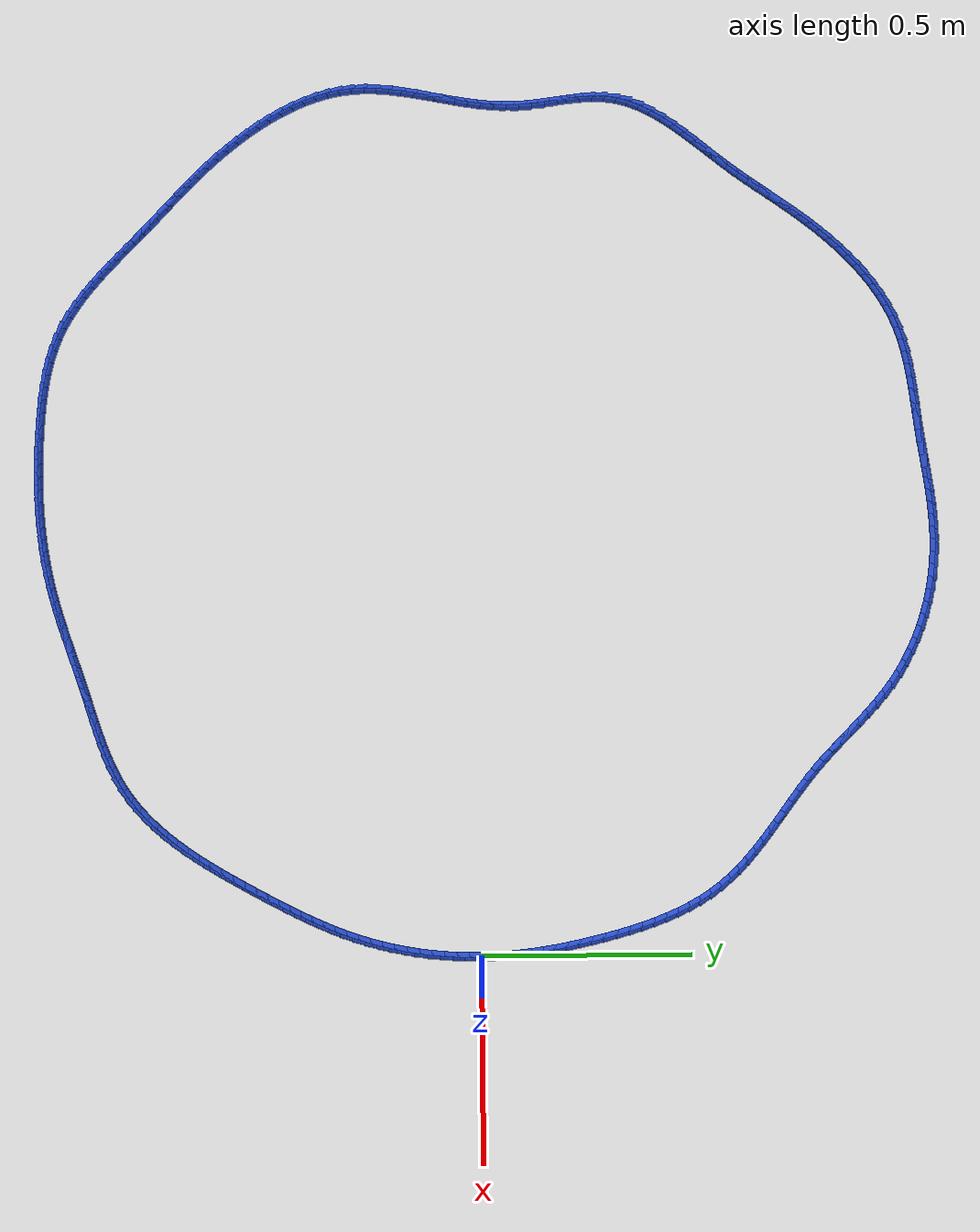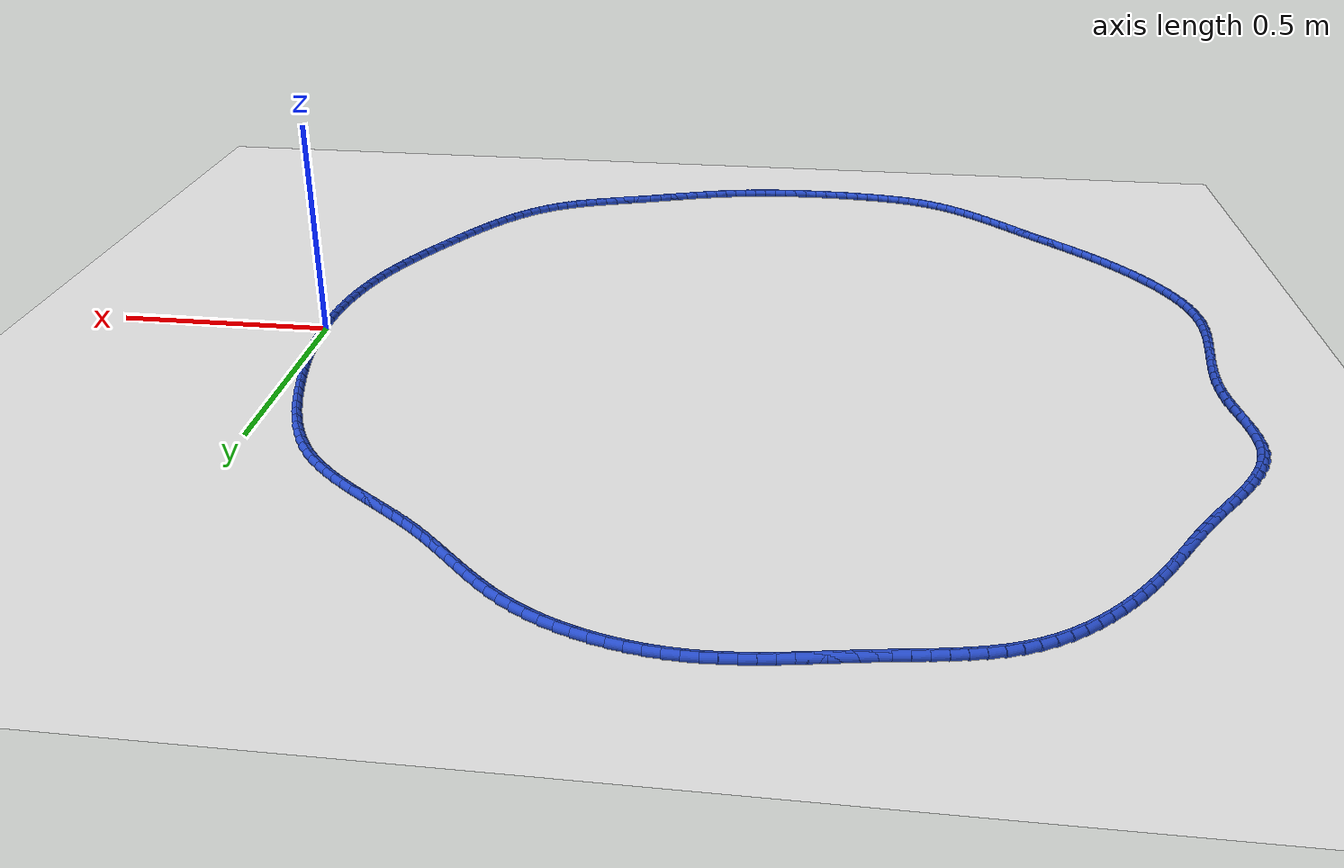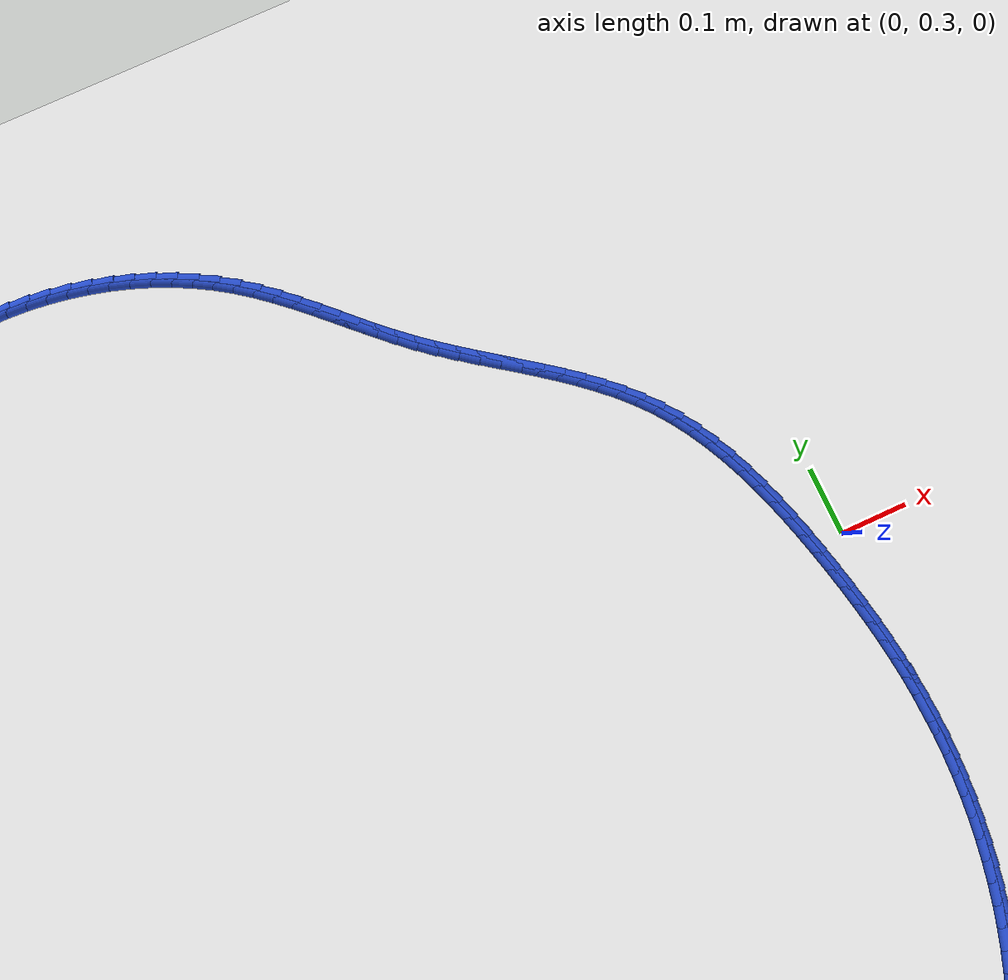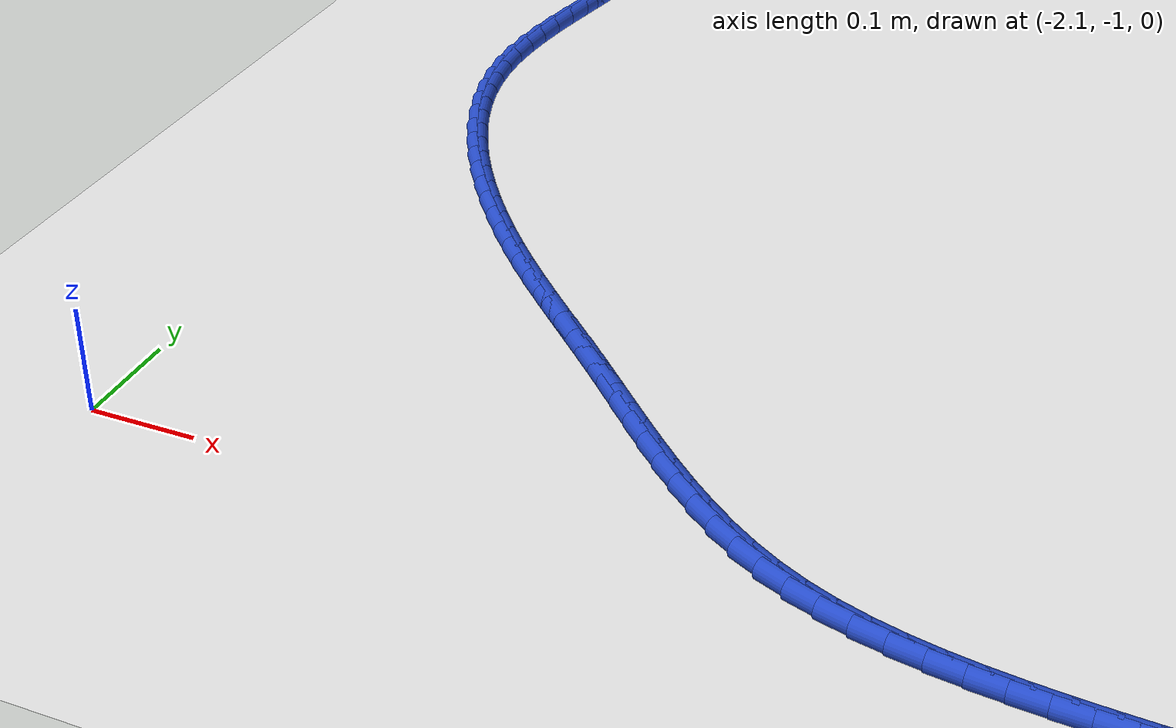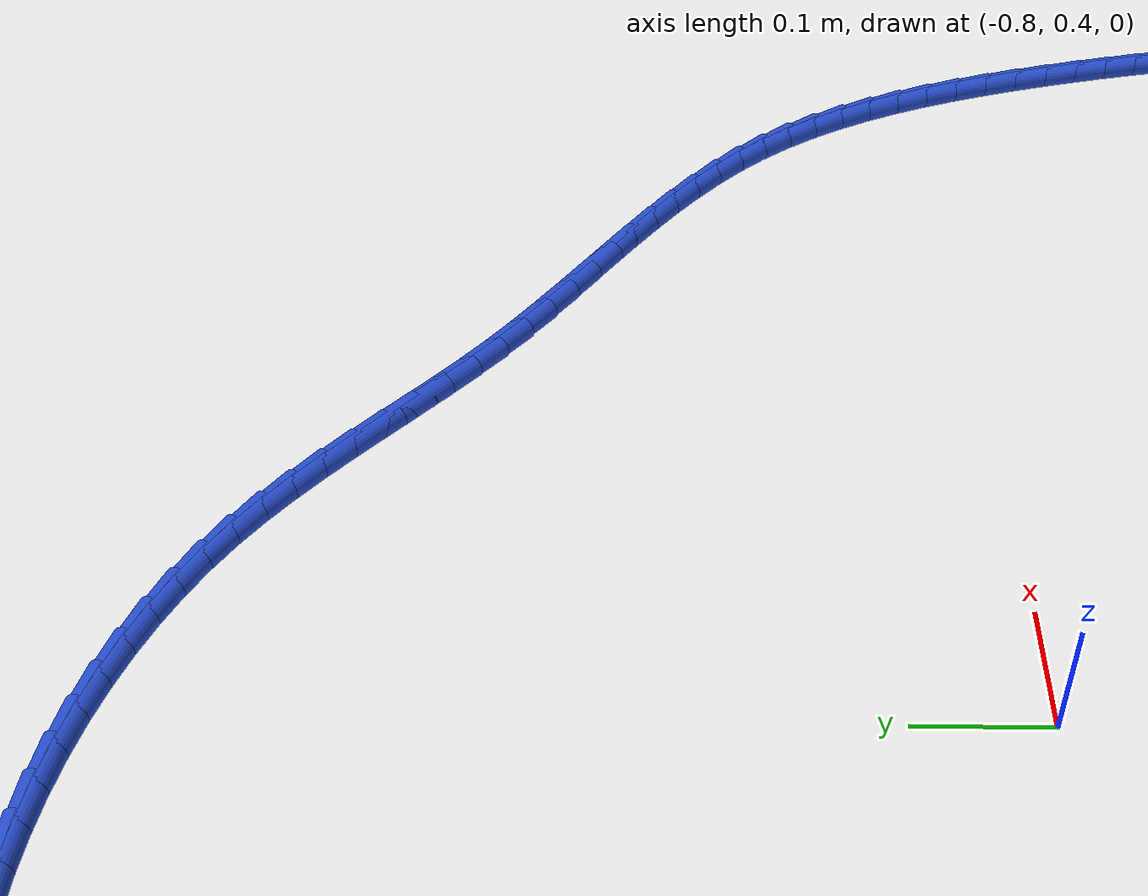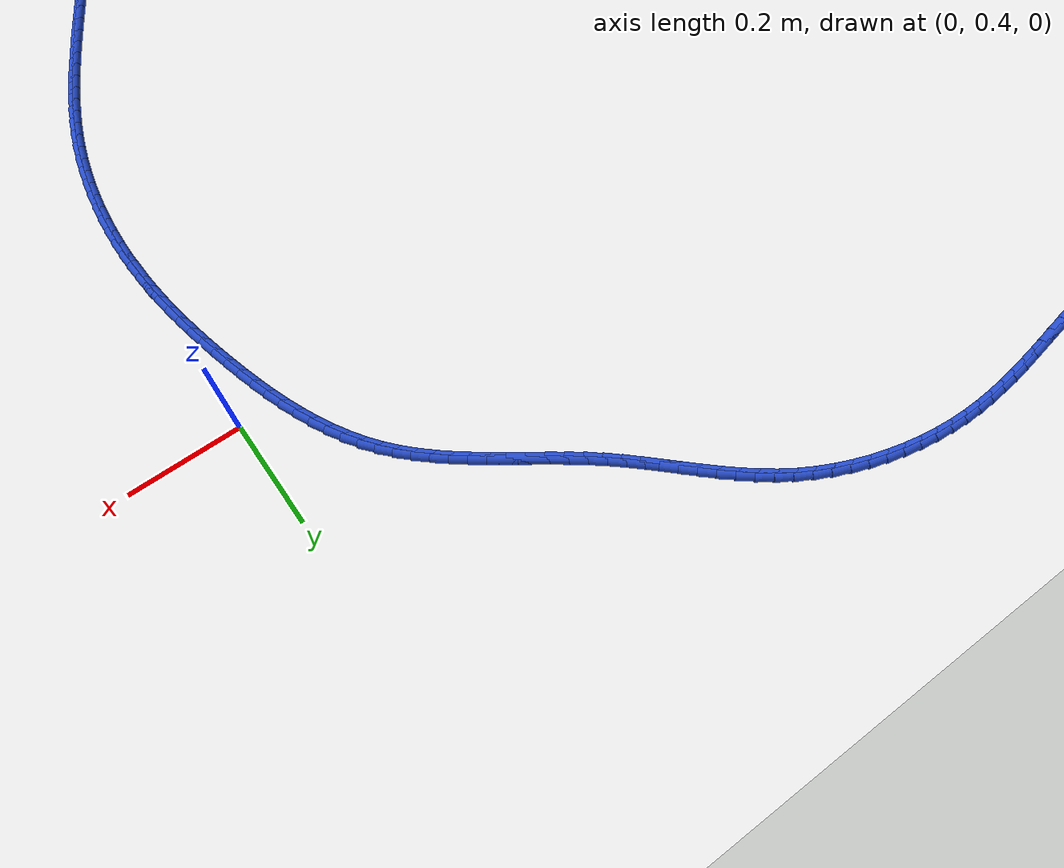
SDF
<sdf version="1.6">
 <world name="default">
  <light name="sun" type="directional">
   <pose>0 0 10 0 -0 0</pose>
   <diffuse>0.8 0.8 0.8 1</diffuse>
   <specular>0.2 0.2 0.2 1</specular>
   <attenuation>
    <range>1000</range>
    <constant>0.9</constant>
    <linear>0.01</linear>
    <quadratic>0.001</quadratic>
   </attenuation>
   <direction>-0.5 0.1 -0.9</direction>
  </light>
  <model name="ground_plane">
   <static>1</static>
   <link name="link">
    <collision name="collision">
     <geometry><plane><normal>0 0 1</normal><size>100 100</size></plane></geometry>
     <surface><friction><ode><mu>100</mu><mu2>50</mu2></ode></friction></surface>
    </collision>
    <visual name="visual">
     <cast_shadows>0</cast_shadows>
     <geometry><plane><normal>0 0 1</normal><size>100 100</size></plane></geometry>
     <material>
      <script><uri>file://media/materials/scripts/gazebo.material</uri><name>Gazebo/WhiteGlow</name></script>
     </material>
    </visual>
   </link>
  </model>
  <gravity>0 0 -9.8</gravity>
  <magnetic_field>6e-06 2.3e-05 -4.2e-05</magnetic_field>
  <atmosphere type="adiabatic"/>
  <physics name="default_physics" default="0" type="ode">
   <max_step_size>0.001</max_step_size>
   <real_time_factor>1</real_time_factor>
   <real_time_update_rate>1000</real_time_update_rate>
  </physics>
  <scene><ambient>0.4 0.4 0.4 1</ambient><background>0.7 0.7 0.7 1</background><shadows>1</shadows></scene>
  <spherical_coordinates>
   <surface_model>EARTH_WGS84</surface_model>
   <latitude_deg>0</latitude_deg>
   <longitude_deg>0</longitude_deg>
   <elevation>0</elevation>
   <heading_deg>0</heading_deg>
  </spherical_coordinates>
  <model name="line">
   <link name="link_0">
    <pose>-3.469446951953614e-18 4.85722573273506e-17 0.01 0 1.57 -1.5418332146010414</pose>
    <collision name="collision">
     <geometry><cylinder><radius>0.01</radius><length>0.08</length></cylinder></geometry>
    </collision>
    <visual name="visual">
     <material>
      <script><name>Gazebo/Blue</name><uri>file://media/materials/scripts/gazebo.material</uri></script>
     </material>
     <geometry><cylinder><radius>0.01</radius><length>0.08</length></cylinder></geometry>
    </visual>
   </link>
   <link name="link_1">
    <pose>-0.0008663245274264614 0.029902942262474204 0.01 0 1.57 -1.510748640837422</pose>
    <collision name="collision">
     <geometry><cylinder><radius>0.01</radius><length>0.08</length></cylinder></geometry>
    </collision>
    <visual name="visual">
     <material>
      <script><name>Gazebo/Blue</name><uri>file://media/materials/scripts/gazebo.material</uri></script>
     </material>
     <geometry><cylinder><radius>0.01</radius><length>0.08</length></cylinder></geometry>
    </visual>
   </link>
   <link name="link_2">
    <pose>-0.002657733682334742 0.05970018589120433 0.01 0 1.57 -1.4812944870312121</pose>
    <collision name="collision">
     <geometry><cylinder><radius>0.01</radius><length>0.08</length></cylinder></geometry>
    </collision>
    <visual name="visual">
     <material>
      <script><name>Gazebo/Blue</name><uri>file://media/materials/scripts/gazebo.material</uri></script>
     </material>
     <geometry><cylinder><radius>0.01</radius><length>0.08</length></cylinder></geometry>
    </visual>
   </link>
   <link name="link_3">
    <pose>-0.00532403409075659 0.08941105075678075 0.01 0 1.57 -1.4535714032352982</pose>
    <collision name="collision">
     <geometry><cylinder><radius>0.01</radius><length>0.08</length></cylinder></geometry>
    </collision>
    <visual name="visual">
     <material>
      <script><name>Gazebo/Blue</name><uri>file://media/materials/scripts/gazebo.material</uri></script>
     </material>
     <geometry><cylinder><radius>0.01</radius><length>0.08</length></cylinder></geometry>
    </visual>
   </link>
   <link name="link_4">
    <pose>-0.008815032378723749 0.11905485672979395 0.01 0 1.57 -1.4276579981320756</pose>
    <collision name="collision">
     <geometry><cylinder><radius>0.01</radius><length>0.08</length></cylinder></geometry>
    </collision>
    <visual name="visual">
     <material>
      <script><name>Gazebo/Blue</name><uri>file://media/materials/scripts/gazebo.material</uri></script>
     </material>
     <geometry><cylinder><radius>0.01</radius><length>0.08</length></cylinder></geometry>
    </visual>
   </link>
   <link name="link_5">
    <pose>-0.013080535172267971 0.14865092368083424 0.01 0 1.57 -1.4036123204927695</pose>
    <collision name="collision">
     <geometry><cylinder><radius>0.01</radius><length>0.08</length></cylinder></geometry>
    </collision>
    <visual name="visual">
     <material>
      <script><name>Gazebo/Blue</name><uri>file://media/materials/scripts/gazebo.material</uri></script>
     </material>
     <geometry><cylinder><radius>0.01</radius><length>0.08</length></cylinder></geometry>
    </visual>
   </link>
   <link name="link_6">
    <pose>-0.018070349097420984 0.178218571480492 0.01 0 1.57 -1.3814738155503965</pose>
    <collision name="collision">
     <geometry><cylinder><radius>0.01</radius><length>0.08</length></cylinder></geometry>
    </collision>
    <visual name="visual">
     <material>
      <script><name>Gazebo/Blue</name><uri>file://media/materials/scripts/gazebo.material</uri></script>
     </material>
     <geometry><cylinder><radius>0.01</radius><length>0.08</length></cylinder></geometry>
    </visual>
   </link>
   <link name="link_7">
    <pose>-0.023734280780214556 0.20777711999935763 0.01 0 1.57 -1.36126556449081</pose>
    <collision name="collision">
     <geometry><cylinder><radius>0.01</radius><length>0.08</length></cylinder></geometry>
    </collision>
    <visual name="visual">
     <material>
      <script><name>Gazebo/Blue</name><uri>file://media/materials/scripts/gazebo.material</uri></script>
     </material>
     <geometry><cylinder><radius>0.01</radius><length>0.08</length></cylinder></geometry>
    </visual>
   </link>
   <link name="link_8">
    <pose>-0.030022136846680418 0.23734588910802162 0.01 0 1.57 -1.34299663909323</pose>
    <collision name="collision">
     <geometry><cylinder><radius>0.01</radius><length>0.08</length></cylinder></geometry>
    </collision>
    <visual name="visual">
     <material>
      <script><name>Gazebo/Blue</name><uri>file://media/materials/scripts/gazebo.material</uri></script>
     </material>
     <geometry><cylinder><radius>0.01</radius><length>0.08</length></cylinder></geometry>
    </visual>
   </link>
   <link name="link_9">
    <pose>-0.03688372392285033 0.2669441986770742 0.01 0 1.57 -1.326536964211542</pose>
    <collision name="collision">
     <geometry><cylinder><radius>0.01</radius><length>0.08</length></cylinder></geometry>
    </collision>
    <visual name="visual">
     <material>
      <script><name>Gazebo/Blue</name><uri>file://media/materials/scripts/gazebo.material</uri></script>
     </material>
     <geometry><cylinder><radius>0.01</radius><length>0.08</length></cylinder></geometry>
    </visual>
   </link>
   <link name="link_10">
    <pose>-0.04427206447080453 0.29658816701202956 0.01 0 1.57 -1.3089412721092473</pose>
    <collision name="collision">
     <geometry><cylinder><radius>0.01</radius><length>0.08</length></cylinder></geometry>
    </collision>
    <visual name="visual">
     <material>
      <script><name>Gazebo/Blue</name><uri>file://media/materials/scripts/gazebo.material</uri></script>
     </material>
     <geometry><cylinder><radius>0.01</radius><length>0.08</length></cylinder></geometry>
    </visual>
   </link>
   <link name="link_11">
    <pose>-0.052213819215632964 0.3262206009412094 0.01 0 1.57 -1.2871938052462488</pose>
    <collision name="collision">
     <geometry><cylinder><radius>0.01</radius><length>0.08</length></cylinder></geometry>
    </collision>
    <visual name="visual">
     <material>
      <script><name>Gazebo/Blue</name><uri>file://media/materials/scripts/gazebo.material</uri></script>
     </material>
     <geometry><cylinder><radius>0.01</radius><length>0.08</length></cylinder></geometry>
    </visual>
   </link>
   <link name="link_12">
    <pose>-0.06080910650710917 0.35571117565244675 0.01 0 1.57 -1.2609926035860026</pose>
    <collision name="collision">
     <geometry><cylinder><radius>0.01</radius><length>0.08</length></cylinder></geometry>
    </collision>
    <visual name="visual">
     <material>
      <script><name>Gazebo/Blue</name><uri>file://media/materials/scripts/gazebo.material</uri></script>
     </material>
     <geometry><cylinder><radius>0.01</radius><length>0.08</length></cylinder></geometry>
    </visual>
   </link>
   <link name="link_13">
    <pose>-0.07016122440332159 0.38492640073590756 0.01 0 1.57 -1.2301064240585315</pose>
    <collision name="collision">
     <geometry><cylinder><radius>0.01</radius><length>0.08</length></cylinder></geometry>
    </collision>
    <visual name="visual">
     <material>
      <script><name>Gazebo/Blue</name><uri>file://media/materials/scripts/gazebo.material</uri></script>
     </material>
     <geometry><cylinder><radius>0.01</radius><length>0.08</length></cylinder></geometry>
    </visual>
   </link>
   <link name="link_14">
    <pose>-0.08037347096235874 0.41373278578175765 0.01 0 1.57 -1.1942597239519621</pose>
    <collision name="collision">
     <geometry><cylinder><radius>0.01</radius><length>0.08</length></cylinder></geometry>
    </collision>
    <visual name="visual">
     <material>
      <script><name>Gazebo/Blue</name><uri>file://media/materials/scripts/gazebo.material</uri></script>
     </material>
     <geometry><cylinder><radius>0.01</radius><length>0.08</length></cylinder></geometry>
    </visual>
   </link>
   <link name="link_15">
    <pose>-0.09154914424230909 0.44199684038016307 0.01 0 1.57 -1.1531484295796557</pose>
    <collision name="collision">
     <geometry><cylinder><radius>0.01</radius><length>0.08</length></cylinder></geometry>
    </collision>
    <visual name="visual">
     <material>
      <script><name>Gazebo/Blue</name><uri>file://media/materials/scripts/gazebo.material</uri></script>
     </material>
     <geometry><cylinder><radius>0.01</radius><length>0.08</length></cylinder></geometry>
    </visual>
   </link>
   <link name="link_16">
    <pose>-0.10379154230126109 0.46958507412128947 0.01 0 1.57 -1.1064630506506774</pose>
    <collision name="collision">
     <geometry><cylinder><radius>0.01</radius><length>0.08</length></cylinder></geometry>
    </collision>
    <visual name="visual">
     <material>
      <script><name>Gazebo/Blue</name><uri>file://media/materials/scripts/gazebo.material</uri></script>
     </material>
     <geometry><cylinder><radius>0.01</radius><length>0.08</length></cylinder></geometry>
    </visual>
   </link>
   <link name="link_17">
    <pose>-0.1172039631973032 0.4963639965953026 0.01 0 1.57 -1.0539219121544394</pose>
    <collision name="collision">
     <geometry><cylinder><radius>0.01</radius><length>0.08</length></cylinder></geometry>
    </collision>
    <visual name="visual">
     <material>
      <script><name>Gazebo/Blue</name><uri>file://media/materials/scripts/gazebo.material</uri></script>
     </material>
     <geometry><cylinder><radius>0.01</radius><length>0.08</length></cylinder></geometry>
    </visual>
   </link>
   <link name="link_18">
    <pose>-0.13188970498852398 0.5222001173923687 0.01 0 1.57 -0.9953167761884901</pose>
    <collision name="collision">
     <geometry><cylinder><radius>0.01</radius><length>0.08</length></cylinder></geometry>
    </collision>
    <visual name="visual">
     <material>
      <script><name>Gazebo/Blue</name><uri>file://media/materials/scripts/gazebo.material</uri></script>
     </material>
     <geometry><cylinder><radius>0.01</radius><length>0.08</length></cylinder></geometry>
    </visual>
   </link>
   <link name="link_19">
    <pose>-0.14795206573301184 0.5469599461026533 0.01 0 1.57 -0.930571358202595</pose>
    <collision name="collision">
     <geometry><cylinder><radius>0.01</radius><length>0.08</length></cylinder></geometry>
    </collision>
    <visual name="visual">
     <material>
      <script><name>Gazebo/Blue</name><uri>file://media/materials/scripts/gazebo.material</uri></script>
     </material>
     <geometry><cylinder><radius>0.01</radius><length>0.08</length></cylinder></geometry>
    </visual>
   </link>
   <link name="link_20">
    <pose>-0.16549434348885528 0.5705099923163224 0.01 0 1.57 -0.862195437643134</pose>
    <collision name="collision">
     <geometry><cylinder><radius>0.01</radius><length>0.08</length></cylinder></geometry>
    </collision>
    <visual name="visual">
     <material>
      <script><name>Gazebo/Blue</name><uri>file://media/materials/scripts/gazebo.material</uri></script>
     </material>
     <geometry><cylinder><radius>0.01</radius><length>0.08</length></cylinder></geometry>
    </visual>
   </link>
   <link name="link_21">
    <pose>-0.18457103720722193 0.5927672783265211 0.01 0 1.57 -0.8004172234152995</pose>
    <collision name="collision">
     <geometry><cylinder><radius>0.01</radius><length>0.08</length></cylinder></geometry>
    </collision>
    <visual name="visual">
     <material>
      <script><name>Gazebo/Blue</name><uri>file://media/materials/scripts/gazebo.material</uri></script>
     </material>
     <geometry><cylinder><radius>0.01</radius><length>0.08</length></cylinder></geometry>
    </visual>
   </link>
   <link name="link_22">
    <pose>-0.2050360613865466 0.6138564544655629 0.01 0 1.57 -0.7481338867954107</pose>
    <collision name="collision">
     <geometry><cylinder><radius>0.01</radius><length>0.08</length></cylinder></geometry>
    </collision>
    <visual name="visual">
     <material>
      <script><name>Gazebo/Blue</name><uri>file://media/materials/scripts/gazebo.material</uri></script>
     </material>
     <geometry><cylinder><radius>0.01</radius><length>0.08</length></cylinder></geometry>
    </visual>
   </link>
   <link name="link_23">
    <pose>-0.22669180043178594 0.6339555106547541 0.01 0 1.57 -0.7054011129285769</pose>
    <collision name="collision">
     <geometry><cylinder><radius>0.01</radius><length>0.08</length></cylinder></geometry>
    </collision>
    <visual name="visual">
     <material>
      <script><name>Gazebo/Blue</name><uri>file://media/materials/scripts/gazebo.material</uri></script>
     </material>
     <geometry><cylinder><radius>0.01</radius><length>0.08</length></cylinder></geometry>
    </visual>
   </link>
   <link name="link_24">
    <pose>-0.2493406387104028 0.6532424368542108 0.01 0 1.57 -0.6720648849168961</pose>
    <collision name="collision">
     <geometry><cylinder><radius>0.01</radius><length>0.08</length></cylinder></geometry>
    </collision>
    <visual name="visual">
     <material>
      <script><name>Gazebo/Blue</name><uri>file://media/materials/scripts/gazebo.material</uri></script>
     </material>
     <geometry><cylinder><radius>0.01</radius><length>0.08</length></cylinder></geometry>
    </visual>
   </link>
   <link name="link_25">
    <pose>-0.27278496058985996 0.6718952230240497 0.01 0 1.57 -0.6478787717977582</pose>
    <collision name="collision">
     <geometry><cylinder><radius>0.01</radius><length>0.08</length></cylinder></geometry>
    </collision>
    <visual name="visual">
     <material>
      <script><name>Gazebo/Blue</name><uri>file://media/materials/scripts/gazebo.material</uri></script>
     </material>
     <geometry><cylinder><radius>0.01</radius><length>0.08</length></cylinder></geometry>
    </visual>
   </link>
   <link name="link_26">
    <pose>-0.2968271504376203 0.6900918591243873 0.01 0 1.57 -0.6325896762150611</pose>
    <collision name="collision">
     <geometry><cylinder><radius>0.01</radius><length>0.08</length></cylinder></geometry>
    </collision>
    <visual name="visual">
     <material>
      <script><name>Gazebo/Blue</name><uri>file://media/materials/scripts/gazebo.material</uri></script>
     </material>
     <geometry><cylinder><radius>0.01</radius><length>0.08</length></cylinder></geometry>
    </visual>
   </link>
   <link name="link_27">
    <pose>-0.3212695926211466 0.7080103351153396 0.01 0 1.57 -0.6259937109540094</pose>
    <collision name="collision">
     <geometry><cylinder><radius>0.01</radius><length>0.08</length></cylinder></geometry>
    </collision>
    <visual name="visual">
     <material>
      <script><name>Gazebo/Blue</name><uri>file://media/materials/scripts/gazebo.material</uri></script>
     </material>
     <geometry><cylinder><radius>0.01</radius><length>0.08</length></cylinder></geometry>
    </visual>
   </link>
   <link name="link_28">
    <pose>-0.34591467150790184 0.7258286409570236 0.01 0 1.57 -0.6279674166619715</pose>
    <collision name="collision">
     <geometry><cylinder><radius>0.01</radius><length>0.08</length></cylinder></geometry>
    </collision>
    <visual name="visual">
     <material>
      <script><name>Gazebo/Blue</name><uri>file://media/materials/scripts/gazebo.material</uri></script>
     </material>
     <geometry><cylinder><radius>0.01</radius><length>0.08</length></cylinder></geometry>
    </visual>
   </link>
   <link name="link_29">
    <pose>-0.37056477146534866 0.7437247666095553 0.01 0 1.57 -0.6384791834148354</pose>
    <collision name="collision">
     <geometry><cylinder><radius>0.01</radius><length>0.08</length></cylinder></geometry>
    </collision>
    <visual name="visual">
     <material>
      <script><name>Gazebo/Blue</name><uri>file://media/materials/scripts/gazebo.material</uri></script>
     </material>
     <geometry><cylinder><radius>0.01</radius><length>0.08</length></cylinder></geometry>
    </visual>
   </link>
   <link name="link_30">
    <pose>-0.39502227686095015 0.7618767020330515 0.01 0 1.57 -0.6575836212396218</pose>
    <collision name="collision">
     <geometry><cylinder><radius>0.01</radius><length>0.08</length></cylinder></geometry>
    </collision>
    <visual name="visual">
     <material>
      <script><name>Gazebo/Blue</name><uri>file://media/materials/scripts/gazebo.material</uri></script>
     </material>
     <geometry><cylinder><radius>0.01</radius><length>0.08</length></cylinder></geometry>
    </visual>
   </link>
   <link name="link_31">
    <pose>-0.419089572062169 0.7804624371876285 0.01 0 1.57 -0.6853990377906917</pose>
    <collision name="collision">
     <geometry><cylinder><radius>0.01</radius><length>0.08</length></cylinder></geometry>
    </collision>
    <visual name="visual">
     <material>
      <script><name>Gazebo/Blue</name><uri>file://media/materials/scripts/gazebo.material</uri></script>
     </material>
     <geometry><cylinder><radius>0.01</radius><length>0.08</length></cylinder></geometry>
    </visual>
   </link>
   <link name="link_32">
    <pose>-0.442569041436468 0.7996599620334026 0.01 0 1.57 -0.7189199640044169</pose>
    <collision name="collision">
     <geometry><cylinder><radius>0.01</radius><length>0.08</length></cylinder></geometry>
    </collision>
    <visual name="visual">
     <material>
      <script><name>Gazebo/Blue</name><uri>file://media/materials/scripts/gazebo.material</uri></script>
     </material>
     <geometry><cylinder><radius>0.01</radius><length>0.08</length></cylinder></geometry>
    </visual>
   </link>
   <link name="link_33">
    <pose>-0.4653297631536652 0.8195792092101718 0.01 0 1.57 -0.745458313184018</pose>
    <collision name="collision">
     <geometry><cylinder><radius>0.01</radius><length>0.08</length></cylinder></geometry>
    </collision>
    <visual name="visual">
     <material>
      <script><name>Gazebo/Blue</name><uri>file://media/materials/scripts/gazebo.material</uri></script>
     </material>
     <geometry><cylinder><radius>0.01</radius><length>0.08</length></cylinder></geometry>
    </visual>
   </link>
   <link name="link_34">
    <pose>-0.4875102850215278 0.8400551325618261 0.01 0 1.57 -0.7617245559441463</pose>
    <collision name="collision">
     <geometry><cylinder><radius>0.01</radius><length>0.08</length></cylinder></geometry>
    </collision>
    <visual name="visual">
     <material>
      <script><name>Gazebo/Blue</name><uri>file://media/materials/scripts/gazebo.material</uri></script>
     </material>
     <geometry><cylinder><radius>0.01</radius><length>0.08</length></cylinder></geometry>
    </visual>
   </link>
   <link name="link_35">
    <pose>-0.5093172026539136 0.8608532469263432 0.01 0 1.57 -0.767667490933275</pose>
    <collision name="collision">
     <geometry><cylinder><radius>0.01</radius><length>0.08</length></cylinder></geometry>
    </collision>
    <visual name="visual">
     <material>
      <script><name>Gazebo/Blue</name><uri>file://media/materials/scripts/gazebo.material</uri></script>
     </material>
     <geometry><cylinder><radius>0.01</radius><length>0.08</length></cylinder></geometry>
    </visual>
   </link>
   <link name="link_36">
    <pose>-0.5309571116672123 0.881739067139117 0.01 0 1.57 -0.7632309427519988</pose>
    <collision name="collision">
     <geometry><cylinder><radius>0.01</radius><length>0.08</length></cylinder></geometry>
    </collision>
    <visual name="visual">
     <material>
      <script><name>Gazebo/Blue</name><uri>file://media/materials/scripts/gazebo.material</uri></script>
     </material>
     <geometry><cylinder><radius>0.01</radius><length>0.08</length></cylinder></geometry>
    </visual>
   </link>
   <link name="link_37">
    <pose>-0.5526366076778138 0.902478108035541 0.01 0 1.57 -0.7483343949049049</pose>
    <collision name="collision">
     <geometry><cylinder><radius>0.01</radius><length>0.08</length></cylinder></geometry>
    </collision>
    <visual name="visual">
     <material>
      <script><name>Gazebo/Blue</name><uri>file://media/materials/scripts/gazebo.material</uri></script>
     </material>
     <geometry><cylinder><radius>0.01</radius><length>0.08</length></cylinder></geometry>
    </visual>
   </link>
   <link name="link_38">
    <pose>-0.5745622863021078 0.9228358844510085 0.01 0 1.57 -0.7228871260414993</pose>
    <collision name="collision">
     <geometry><cylinder><radius>0.01</radius><length>0.08</length></cylinder></geometry>
    </collision>
    <visual name="visual">
     <material>
      <script><name>Gazebo/Blue</name><uri>file://media/materials/scripts/gazebo.material</uri></script>
     </material>
     <geometry><cylinder><radius>0.01</radius><length>0.08</length></cylinder></geometry>
    </visual>
   </link>
   <link name="link_39">
    <pose>-0.5969407431564845 0.9425779112209136 0.01 0 1.57 -0.6868376550283946</pose>
    <collision name="collision">
     <geometry><cylinder><radius>0.01</radius><length>0.08</length></cylinder></geometry>
    </collision>
    <visual name="visual">
     <material>
      <script><name>Gazebo/Blue</name><uri>file://media/materials/scripts/gazebo.material</uri></script>
     </material>
     <geometry><cylinder><radius>0.01</radius><length>0.08</length></cylinder></geometry>
    </visual>
   </link>
   <link name="link_40">
    <pose>-0.6199785738573335 0.9614697031806507 0.01 0 1.57 -0.64025954629374</pose>
    <collision name="collision">
     <geometry><cylinder><radius>0.01</radius><length>0.08</length></cylinder></geometry>
    </collision>
    <visual name="visual">
     <material>
      <script><name>Gazebo/Blue</name><uri>file://media/materials/scripts/gazebo.material</uri></script>
     </material>
     <geometry><cylinder><radius>0.01</radius><length>0.08</length></cylinder></geometry>
    </visual>
   </link>
   <link name="link_41">
    <pose>-0.6438823740210443 0.9792767751656118 0.01 0 1.57 -0.5839731546389376</pose>
    <collision name="collision">
     <geometry><cylinder><radius>0.01</radius><length>0.08</length></cylinder></geometry>
    </collision>
    <visual name="visual">
     <material>
      <script><name>Gazebo/Blue</name><uri>file://media/materials/scripts/gazebo.material</uri></script>
     </material>
     <geometry><cylinder><radius>0.01</radius><length>0.08</length></cylinder></geometry>
    </visual>
   </link>
   <link name="link_42">
    <pose>-0.6688451532940108 0.995773725241336 0.01 0 1.57 -0.5251536760143889</pose>
    <collision name="collision">
     <geometry><cylinder><radius>0.01</radius><length>0.08</length></cylinder></geometry>
    </collision>
    <visual name="visual">
     <material>
      <script><name>Gazebo/Blue</name><uri>file://media/materials/scripts/gazebo.material</uri></script>
     </material>
     <geometry><cylinder><radius>0.01</radius><length>0.08</length></cylinder></geometry>
    </visual>
   </link>
   <link name="link_43">
    <pose>-0.6948771692671671 1.0108573347977479 0.01 0 1.57 -0.468505167271352</pose>
    <collision name="collision">
     <geometry><cylinder><radius>0.01</radius><length>0.08</length></cylinder></geometry>
    </collision>
    <visual name="visual">
     <material>
      <script><name>Gazebo/Blue</name><uri>file://media/materials/scripts/gazebo.material</uri></script>
     </material>
     <geometry><cylinder><radius>0.01</radius><length>0.08</length></cylinder></geometry>
    </visual>
   </link>
   <link name="link_44">
    <pose>-0.7218578107339338 1.0245118807371931 0.01 0 1.57 -0.4138168235199364</pose>
    <collision name="collision">
     <geometry><cylinder><radius>0.01</radius><length>0.08</length></cylinder></geometry>
    </collision>
    <visual name="visual">
     <material>
      <script><name>Gazebo/Blue</name><uri>file://media/materials/scripts/gazebo.material</uri></script>
     </material>
     <geometry><cylinder><radius>0.01</radius><length>0.08</length></cylinder></geometry>
    </visual>
   </link>
   <link name="link_45">
    <pose>-0.7496636212663554 1.0367235422038583 0.01 0 1.57 -0.3607569520621443</pose>
    <collision name="collision">
     <geometry><cylinder><radius>0.01</radius><length>0.08</length></cylinder></geometry>
    </collision>
    <visual name="visual">
     <material>
      <script><name>Gazebo/Blue</name><uri>file://media/materials/scripts/gazebo.material</uri></script>
     </material>
     <geometry><cylinder><radius>0.01</radius><length>0.08</length></cylinder></geometry>
    </visual>
   </link>
   <link name="link_46">
    <pose>-0.778171144436476 1.0474784983419307 0.01 0 1.57 -0.3089848614489075</pose>
    <collision name="collision">
     <geometry><cylinder><radius>0.01</radius><length>0.08</length></cylinder></geometry>
    </collision>
    <visual name="visual">
     <material>
      <script><name>Gazebo/Blue</name><uri>file://media/materials/scripts/gazebo.material</uri></script>
     </material>
     <geometry><cylinder><radius>0.01</radius><length>0.08</length></cylinder></geometry>
    </visual>
   </link>
   <link name="link_47">
    <pose>-0.8072569238163396 1.0567629282955966 0.01 0 1.57 -0.2581544715538874</pose>
    <collision name="collision">
     <geometry><cylinder><radius>0.01</radius><length>0.08</length></cylinder></geometry>
    </collision>
    <visual name="visual">
     <material>
      <script><name>Gazebo/Blue</name><uri>file://media/materials/scripts/gazebo.material</uri></script>
     </material>
     <geometry><cylinder><radius>0.01</radius><length>0.08</length></cylinder></geometry>
    </visual>
   </link>
   <link name="link_48">
    <pose>-0.8367975029779905 1.0645630112090427 0.01 0 1.57 -0.2079157711107662</pose>
    <collision name="collision">
     <geometry><cylinder><radius>0.01</radius><length>0.08</length></cylinder></geometry>
    </collision>
    <visual name="visual">
     <material>
      <script><name>Gazebo/Blue</name><uri>file://media/materials/scripts/gazebo.material</uri></script>
     </material>
     <geometry><cylinder><radius>0.01</radius><length>0.08</length></cylinder></geometry>
    </visual>
   </link>
   <link name="link_49">
    <pose>-0.8666694254934733 1.070864926226456 0.01 0 1.57 -0.15791470929435678</pose>
    <collision name="collision">
     <geometry><cylinder><radius>0.01</radius><length>0.08</length></cylinder></geometry>
    </collision>
    <visual name="visual">
     <material>
      <script><name>Gazebo/Blue</name><uri>file://media/materials/scripts/gazebo.material</uri></script>
     </material>
     <geometry><cylinder><radius>0.01</radius><length>0.08</length></cylinder></geometry>
    </visual>
   </link>
   <link name="link_50">
    <pose>-0.8967492349348317 1.0756548524920237 0.01 0 1.57 -0.10779203466109578</pose>
    <collision name="collision">
     <geometry><cylinder><radius>0.01</radius><length>0.08</length></cylinder></geometry>
    </collision>
    <visual name="visual">
     <material>
      <script><name>Gazebo/Blue</name><uri>file://media/materials/scripts/gazebo.material</uri></script>
     </material>
     <geometry><cylinder><radius>0.01</radius><length>0.08</length></cylinder></geometry>
    </visual>
   </link>
   <link name="link_51">
    <pose>-0.92691347487411 1.0789189691499321 0.01 0 1.57 -0.05718154400220344</pose>
    <collision name="collision">
     <geometry><cylinder><radius>0.01</radius><length>0.08</length></cylinder></geometry>
    </collision>
    <visual name="visual">
     <material>
      <script><name>Gazebo/Blue</name><uri>file://media/materials/scripts/gazebo.material</uri></script>
     </material>
     <geometry><cylinder><radius>0.01</radius><length>0.08</length></cylinder></geometry>
    </visual>
   </link>
   <link name="link_52">
    <pose>-0.9570386888833529 1.0806434553443682 0.01 0 1.57 -0.006690251038141633</pose>
    <collision name="collision">
     <geometry><cylinder><radius>0.01</radius><length>0.08</length></cylinder></geometry>
    </collision>
    <visual name="visual">
     <material>
      <script><name>Gazebo/Blue</name><uri>file://media/materials/scripts/gazebo.material</uri></script>
     </material>
     <geometry><cylinder><radius>0.01</radius><length>0.08</length></cylinder></geometry>
    </visual>
   </link>
   <link name="link_53">
    <pose>-0.9870229140947362 1.0808440603312157 0.01 0 1.57 0.039003583011314756</pose>
    <collision name="collision">
     <geometry><cylinder><radius>0.01</radius><length>0.08</length></cylinder></geometry>
    </collision>
    <visual name="visual">
     <material>
      <script><name>Gazebo/Blue</name><uri>file://media/materials/scripts/gazebo.material</uri></script>
     </material>
     <geometry><cylinder><radius>0.01</radius><length>0.08</length></cylinder></geometry>
    </visual>
   </link>
   <link name="link_54">
    <pose>-1.0168680349902326 1.0796794030312264 0.01 0 1.57 0.07812813988375267</pose>
    <collision name="collision">
     <geometry><cylinder><radius>0.01</radius><length>0.08</length></cylinder></geometry>
    </collision>
    <visual name="visual">
     <material>
      <script><name>Gazebo/Blue</name><uri>file://media/materials/scripts/gazebo.material</uri></script>
     </material>
     <geometry><cylinder><radius>0.01</radius><length>0.08</length></cylinder></geometry>
    </visual>
   </link>
   <link name="link_55">
    <pose>-1.0466072578297188 1.0773511938058198 0.01 0 1.57 0.11044944147505356</pose>
    <collision name="collision">
     <geometry><cylinder><radius>0.01</radius><length>0.08</length></cylinder></geometry>
    </collision>
    <visual name="visual">
     <material>
      <script><name>Gazebo/Blue</name><uri>file://media/materials/scripts/gazebo.material</uri></script>
     </material>
     <geometry><cylinder><radius>0.01</radius><length>0.08</length></cylinder></geometry>
    </visual>
   </link>
   <link name="link_56">
    <pose>-1.0762737953448058 1.0740611519200096 0.01 0 1.57 0.13586241205830019</pose>
    <collision name="collision">
     <geometry><cylinder><radius>0.01</radius><length>0.08</length></cylinder></geometry>
    </collision>
    <visual name="visual">
     <material>
      <script><name>Gazebo/Blue</name><uri>file://media/materials/scripts/gazebo.material</uri></script>
     </material>
     <geometry><cylinder><radius>0.01</radius><length>0.08</length></cylinder></geometry>
    </visual>
   </link>
   <link name="link_57">
    <pose>-1.1059008602671065 1.0700109966388092 0.01 0 1.57 0.15434740777895228</pose>
    <collision name="collision">
     <geometry><cylinder><radius>0.01</radius><length>0.08</length></cylinder></geometry>
    </collision>
    <visual name="visual">
     <material>
      <script><name>Gazebo/Blue</name><uri>file://media/materials/scripts/gazebo.material</uri></script>
     </material>
     <geometry><cylinder><radius>0.01</radius><length>0.08</length></cylinder></geometry>
    </visual>
   </link>
   <link name="link_58">
    <pose>-1.135521665328232 1.0654024472272323 0.01 0 1.57 0.1659339457174354</pose>
    <collision name="collision">
     <geometry><cylinder><radius>0.01</radius><length>0.08</length></cylinder></geometry>
    </collision>
    <visual name="visual">
     <material>
      <script><name>Gazebo/Blue</name><uri>file://media/materials/scripts/gazebo.material</uri></script>
     </material>
     <geometry><cylinder><radius>0.01</radius><length>0.08</length></cylinder></geometry>
    </visual>
   </link>
   <link name="link_59">
    <pose>-1.165169423259795 1.060437222950293 0.01 0 1.57 0.17067388880014298</pose>
    <collision name="collision">
     <geometry><cylinder><radius>0.01</radius><length>0.08</length></cylinder></geometry>
    </collision>
    <visual name="visual">
     <material>
      <script><name>Gazebo/Blue</name><uri>file://media/materials/scripts/gazebo.material</uri></script>
     </material>
     <geometry><cylinder><radius>0.01</radius><length>0.08</length></cylinder></geometry>
    </visual>
   </link>
   <link name="link_60">
    <pose>-1.194877346793406 1.0553170430730041 0.01 0 1.57 0.16862479535718097</pose>
    <collision name="collision">
     <geometry><cylinder><radius>0.01</radius><length>0.08</length></cylinder></geometry>
    </collision>
    <visual name="visual">
     <material>
      <script><name>Gazebo/Blue</name><uri>file://media/materials/scripts/gazebo.material</uri></script>
     </material>
     <geometry><cylinder><radius>0.01</radius><length>0.08</length></cylinder></geometry>
    </visual>
   </link>
   <link name="link_61">
    <pose>-1.2246786486606784 1.0502436268603799 0.01 0 1.57 0.1598436374152835</pose>
    <collision name="collision">
     <geometry><cylinder><radius>0.01</radius><length>0.08</length></cylinder></geometry>
    </collision>
    <visual name="visual">
     <material>
      <script><name>Gazebo/Blue</name><uri>file://media/materials/scripts/gazebo.material</uri></script>
     </material>
     <geometry><cylinder><radius>0.01</radius><length>0.08</length></cylinder></geometry>
    </visual>
   </link>
   <link name="link_62">
    <pose>-1.254606538009798 1.045418681569717 0.01 0 1.57 0.14772607011314776</pose>
    <collision name="collision">
     <geometry><cylinder><radius>0.01</radius><length>0.08</length></cylinder></geometry>
    </collision>
    <visual name="visual">
     <material>
      <script><name>Gazebo/Blue</name><uri>file://media/materials/scripts/gazebo.material</uri></script>
     </material>
     <geometry><cylinder><radius>0.01</radius><length>0.08</length></cylinder></geometry>
    </visual>
   </link>
   <link name="link_63">
    <pose>-1.2846649113978192 1.0409456907440309 0.01 0 1.57 0.1436783478197789</pose>
    <collision name="collision">
     <geometry><cylinder><radius>0.01</radius><length>0.08</length></cylinder></geometry>
    </collision>
    <visual name="visual">
     <material>
      <script><name>Gazebo/Blue</name><uri>file://media/materials/scripts/gazebo.material</uri></script>
     </material>
     <geometry><cylinder><radius>0.01</radius><length>0.08</length></cylinder></geometry>
    </visual>
   </link>
   <link name="link_64">
    <pose>-1.3147573697299255 1.0365920567041698 0.01 0 1.57 0.15010824287036018</pose>
    <collision name="collision">
     <geometry><cylinder><radius>0.01</radius><length>0.08</length></cylinder></geometry>
    </collision>
    <visual name="visual">
     <material>
      <script><name>Gazebo/Blue</name><uri>file://media/materials/scripts/gazebo.material</uri></script>
     </material>
     <geometry><cylinder><radius>0.01</radius><length>0.08</length></cylinder></geometry>
    </visual>
   </link>
   <link name="link_65">
    <pose>-1.3447660807107054 1.0320533611474891 0.01 0 1.57 0.16711701678033428</pose>
    <collision name="collision">
     <geometry><cylinder><radius>0.01</radius><length>0.08</length></cylinder></geometry>
    </collision>
    <visual name="visual">
     <material>
      <script><name>Gazebo/Blue</name><uri>file://media/materials/scripts/gazebo.material</uri></script>
     </material>
     <geometry><cylinder><radius>0.01</radius><length>0.08</length></cylinder></geometry>
    </visual>
   </link>
   <link name="link_66">
    <pose>-1.374573212044747 1.0270251857713428 0.01 0 1.57 0.19493340738143822</pose>
    <collision name="collision">
     <geometry><cylinder><radius>0.01</radius><length>0.08</length></cylinder></geometry>
    </collision>
    <visual name="visual">
     <material>
      <script><name>Gazebo/Blue</name><uri>file://media/materials/scripts/gazebo.material</uri></script>
     </material>
     <geometry><cylinder><radius>0.01</radius><length>0.08</length></cylinder></geometry>
    </visual>
   </link>
   <link name="link_67">
    <pose>-1.4040609314366386 1.0212031122730865 0.01 0 1.57 0.2338607814405703</pose>
    <collision name="collision">
     <geometry><cylinder><radius>0.01</radius><length>0.08</length></cylinder></geometry>
    </collision>
    <visual name="visual">
     <material>
      <script><name>Gazebo/Blue</name><uri>file://media/materials/scripts/gazebo.material</uri></script>
     </material>
     <geometry><cylinder><radius>0.01</radius><length>0.08</length></cylinder></geometry>
    </visual>
   </link>
   <link name="link_68">
    <pose>-1.433111406590969 1.0142827223500746 0.01 0 1.57 0.2841810939001059</pose>
    <collision name="collision">
     <geometry><cylinder><radius>0.01</radius><length>0.08</length></cylinder></geometry>
    </collision>
    <visual name="visual">
     <material>
      <script><name>Gazebo/Blue</name><uri>file://media/materials/scripts/gazebo.material</uri></script>
     </material>
     <geometry><cylinder><radius>0.01</radius><length>0.08</length></cylinder></geometry>
    </visual>
   </link>
   <link name="link_69">
    <pose>-1.4616068052123259 1.0059595976996625 0.01 0 1.57 0.3460067363156256</pose>
    <collision name="collision">
     <geometry><cylinder><radius>0.01</radius><length>0.08</length></cylinder></geometry>
    </collision>
    <visual name="visual">
     <material>
      <script><name>Gazebo/Blue</name><uri>file://media/materials/scripts/gazebo.material</uri></script>
     </material>
     <geometry><cylinder><radius>0.01</radius><length>0.08</length></cylinder></geometry>
    </visual>
   </link>
   <link name="link_70">
    <pose>-1.4894292950052985 0.9959293200192045 0.01 0 1.57 0.4182340303166367</pose>
    <collision name="collision">
     <geometry><cylinder><radius>0.01</radius><length>0.08</length></cylinder></geometry>
    </collision>
    <visual name="visual">
     <material>
      <script><name>Gazebo/Blue</name><uri>file://media/materials/scripts/gazebo.material</uri></script>
     </material>
     <geometry><cylinder><radius>0.01</radius><length>0.08</length></cylinder></geometry>
    </visual>
   </link>
   <link name="link_71">
    <pose>-1.5164669979196208 0.983912249071872 0.01 0 1.57 0.4907335295005106</pose>
    <collision name="collision">
     <geometry><cylinder><radius>0.01</radius><length>0.08</length></cylinder></geometry>
    </collision>
    <visual name="visual">
     <material>
      <script><name>Gazebo/Blue</name><uri>file://media/materials/scripts/gazebo.material</uri></script>
     </material>
     <geometry><cylinder><radius>0.01</radius><length>0.08</length></cylinder></geometry>
    </visual>
   </link>
   <link name="link_72">
    <pose>-1.5426752338772993 0.9699083830533397 0.01 0 1.57 0.5572904909467037</pose>
    <collision name="collision">
     <geometry><cylinder><radius>0.01</radius><length>0.08</length></cylinder></geometry>
    </collision>
    <visual name="visual">
     <material>
      <script><name>Gazebo/Blue</name><uri>file://media/materials/scripts/gazebo.material</uri></script>
     </material>
     <geometry><cylinder><radius>0.01</radius><length>0.08</length></cylinder></geometry>
    </visual>
   </link>
   <link name="link_73">
    <pose>-1.568051735982884 0.9540942188761956 0.01 0 1.57 0.6179351739986538</pose>
    <collision name="collision">
     <geometry><cylinder><radius>0.01</radius><length>0.08</length></cylinder></geometry>
    </collision>
    <visual name="visual">
     <material>
      <script><name>Gazebo/Blue</name><uri>file://media/materials/scripts/gazebo.material</uri></script>
     </material>
     <geometry><cylinder><radius>0.01</radius><length>0.08</length></cylinder></geometry>
    </visual>
   </link>
   <link name="link_74">
    <pose>-1.5925949031556852 0.9366490241823976 0.01 0 1.57 0.6729476169263701</pose>
    <collision name="collision">
     <geometry><cylinder><radius>0.01</radius><length>0.08</length></cylinder></geometry>
    </collision>
    <visual name="visual">
     <material>
      <script><name>Gazebo/Blue</name><uri>file://media/materials/scripts/gazebo.material</uri></script>
     </material>
     <geometry><cylinder><radius>0.01</radius><length>0.08</length></cylinder></geometry>
    </visual>
   </link>
   <link name="link_75">
    <pose>-1.6163031343150116 0.9177520666139047 0.01 0 1.57 0.722697715492305</pose>
    <collision name="collision">
     <geometry><cylinder><radius>0.01</radius><length>0.08</length></cylinder></geometry>
    </collision>
    <visual name="visual">
     <material>
      <script><name>Gazebo/Blue</name><uri>file://media/materials/scripts/gazebo.material</uri></script>
     </material>
     <geometry><cylinder><radius>0.01</radius><length>0.08</length></cylinder></geometry>
    </visual>
   </link>
   <link name="link_76">
    <pose>-1.6391748283801735 0.8975826138126752 0.01 0 1.57 0.7675953675321195</pose>
    <collision name="collision">
     <geometry><cylinder><radius>0.01</radius><length>0.08</length></cylinder></geometry>
    </collision>
    <visual name="visual">
     <material>
      <script><name>Gazebo/Blue</name><uri>file://media/materials/scripts/gazebo.material</uri></script>
     </material>
     <geometry><cylinder><radius>0.01</radius><length>0.08</length></cylinder></geometry>
    </visual>
   </link>
   <link name="link_77">
    <pose>-1.661208384270481 0.8763199334206684 0.01 0 1.57 0.8080554188407614</pose>
    <collision name="collision">
     <geometry><cylinder><radius>0.01</radius><length>0.08</length></cylinder></geometry>
    </collision>
    <visual name="visual">
     <material>
      <script><name>Gazebo/Blue</name><uri>file://media/materials/scripts/gazebo.material</uri></script>
     </material>
     <geometry><cylinder><radius>0.01</radius><length>0.08</length></cylinder></geometry>
    </visual>
   </link>
   <link name="link_78">
    <pose>-1.6824022009052444 0.8541432930798424 0.01 0 1.57 0.8444747652360617</pose>
    <collision name="collision">
     <geometry><cylinder><radius>0.01</radius><length>0.08</length></cylinder></geometry>
    </collision>
    <visual name="visual">
     <material>
      <script><name>Gazebo/Blue</name><uri>file://media/materials/scripts/gazebo.material</uri></script>
     </material>
     <geometry><cylinder><radius>0.01</radius><length>0.08</length></cylinder></geometry>
    </visual>
   </link>
   <link name="link_79">
    <pose>-1.7027546772037716 0.8312319604321562 0.01 0 1.57 0.87721844168977</pose>
    <collision name="collision">
     <geometry><cylinder><radius>0.01</radius><length>0.08</length></cylinder></geometry>
    </collision>
    <visual name="visual">
     <material>
      <script><name>Gazebo/Blue</name><uri>file://media/materials/scripts/gazebo.material</uri></script>
     </material>
     <geometry><cylinder><radius>0.01</radius><length>0.08</length></cylinder></geometry>
    </visual>
   </link>
   <link name="link_80">
    <pose>-1.7222642120853742 0.8077652031195677 0.01 0 1.57 0.9066101463321842</pose>
    <collision name="collision">
     <geometry><cylinder><radius>0.01</radius><length>0.08</length></cylinder></geometry>
    </collision>
    <visual name="visual">
     <material>
      <script><name>Gazebo/Blue</name><uri>file://media/materials/scripts/gazebo.material</uri></script>
     </material>
     <geometry><cylinder><radius>0.01</radius><length>0.08</length></cylinder></geometry>
    </visual>
   </link>
   <link name="link_81">
    <pose>-1.7409293390851568 0.7839221978528693 0.01 0 1.57 0.9321950477538616</pose>
    <collision name="collision">
     <geometry><cylinder><radius>0.01</radius><length>0.08</length></cylinder></geometry>
    </collision>
    <visual name="visual">
     <material>
      <script><name>Gazebo/Blue</name><uri>file://media/materials/scripts/gazebo.material</uri></script>
     </material>
     <geometry><cylinder><radius>0.01</radius><length>0.08</length></cylinder></geometry>
    </visual>
   </link>
   <link name="link_82">
    <pose>-1.7588036060606096 0.7598449599049348 0.01 0 1.57 0.9520445798185945</pose>
    <collision name="collision">
     <geometry><cylinder><radius>0.01</radius><length>0.08</length></cylinder></geometry>
    </collision>
    <visual name="visual">
     <material>
      <script><name>Gazebo/Blue</name><uri>file://media/materials/scripts/gazebo.material</uri></script>
     </material>
     <geometry><cylinder><radius>0.01</radius><length>0.08</length></cylinder></geometry>
    </visual>
   </link>
   <link name="link_83">
    <pose>-1.7760799184387348 0.7355813703769674 0.01 0 1.57 0.9655535357585275</pose>
    <collision name="collision">
     <geometry><cylinder><radius>0.01</radius><length>0.08</length></cylinder></geometry>
    </collision>
    <visual name="visual">
     <material>
      <script><name>Gazebo/Blue</name><uri>file://media/materials/scripts/gazebo.material</uri></script>
     </material>
     <geometry><cylinder><radius>0.01</radius><length>0.08</length></cylinder></geometry>
    </visual>
   </link>
   <link name="link_84">
    <pose>-1.7929729142200395 0.71116463030785 0.01 0 1.57 0.972523341493911</pose>
    <collision name="collision">
     <geometry><cylinder><radius>0.01</radius><length>0.08</length></cylinder></geometry>
    </collision>
    <visual name="visual">
     <material>
      <script><name>Gazebo/Blue</name><uri>file://media/materials/scripts/gazebo.material</uri></script>
     </material>
     <geometry><cylinder><radius>0.01</radius><length>0.08</length></cylinder></geometry>
    </visual>
   </link>
   <link name="link_85">
    <pose>-1.8096972314050328 0.6866279407364648 0.01 0 1.57 0.9728885904679772</pose>
    <collision name="collision">
     <geometry><cylinder><radius>0.01</radius><length>0.08</length></cylinder></geometry>
    </collision>
    <visual name="visual">
     <material>
      <script><name>Gazebo/Blue</name><uri>file://media/materials/scripts/gazebo.material</uri></script>
     </material>
     <geometry><cylinder><radius>0.01</radius><length>0.08</length></cylinder></geometry>
    </visual>
   </link>
   <link name="link_86">
    <pose>-1.8264675079942219 0.662004502701695 0.01 0 1.57 0.9667102960204816</pose>
    <collision name="collision">
     <geometry><cylinder><radius>0.01</radius><length>0.08</length></cylinder></geometry>
    </collision>
    <visual name="visual">
     <material>
      <script><name>Gazebo/Blue</name><uri>file://media/materials/scripts/gazebo.material</uri></script>
     </material>
     <geometry><cylinder><radius>0.01</radius><length>0.08</length></cylinder></geometry>
    </visual>
   </link>
   <link name="link_87">
    <pose>-1.8434983819881154 0.6373275172424226 0.01 0 1.57 0.9541714424767621</pose>
    <collision name="collision">
     <geometry><cylinder><radius>0.01</radius><length>0.08</length></cylinder></geometry>
    </collision>
    <visual name="visual">
     <material>
      <script><name>Gazebo/Blue</name><uri>file://media/materials/scripts/gazebo.material</uri></script>
     </material>
     <geometry><cylinder><radius>0.01</radius><length>0.08</length></cylinder></geometry>
    </visual>
   </link>
   <link name="link_88">
    <pose>-1.8610044913872208 0.6126301853975303 0.01 0 1.57 0.935593271071417</pose>
    <collision name="collision">
     <geometry><cylinder><radius>0.01</radius><length>0.08</length></cylinder></geometry>
    </collision>
    <visual name="visual">
     <material>
      <script><name>Gazebo/Blue</name><uri>file://media/materials/scripts/gazebo.material</uri></script>
     </material>
     <geometry><cylinder><radius>0.01</radius><length>0.08</length></cylinder></geometry>
    </visual>
   </link>
   <link name="link_89">
    <pose>-1.8791998461633614 0.587945604660771 0.01 0 1.57 0.9163313343535722</pose>
    <collision name="collision">
     <geometry><cylinder><radius>0.01</radius><length>0.08</length></cylinder></geometry>
    </collision>
    <visual name="visual">
     <material>
      <script><name>Gazebo/Blue</name><uri>file://media/materials/scripts/gazebo.material</uri></script>
     </material>
     <geometry><cylinder><radius>0.01</radius><length>0.08</length></cylinder></geometry>
    </visual>
   </link>
   <link name="link_90">
    <pose>-1.8981262805609707 0.5632784853543079 0.01 0 1.57 0.9078971553911593</pose>
    <collision name="collision">
     <geometry><cylinder><radius>0.01</radius><length>0.08</length></cylinder></geometry>
    </collision>
    <visual name="visual">
     <material>
      <script><name>Gazebo/Blue</name><uri>file://media/materials/scripts/gazebo.material</uri></script>
     </material>
     <geometry><cylinder><radius>0.01</radius><length>0.08</length></cylinder></geometry>
    </visual>
   </link>
   <link name="link_91">
    <pose>-1.9174202712299586 0.5385667051766511 0.01 0 1.57 0.9115392157638947</pose>
    <collision name="collision">
     <geometry><cylinder><radius>0.01</radius><length>0.08</length></cylinder></geometry>
    </collision>
    <visual name="visual">
     <material>
      <script><name>Gazebo/Blue</name><uri>file://media/materials/scripts/gazebo.material</uri></script>
     </material>
     <geometry><cylinder><radius>0.01</radius><length>0.08</length></cylinder></geometry>
    </visual>
   </link>
   <link name="link_92">
    <pose>-1.9366600018459328 0.5137385308742393 0.01 0 1.57 0.9272586865867808</pose>
    <collision name="collision">
     <geometry><cylinder><radius>0.01</radius><length>0.08</length></cylinder></geometry>
    </collision>
    <visual name="visual">
     <material>
      <script><name>Gazebo/Blue</name><uri>file://media/materials/scripts/gazebo.material</uri></script>
     </material>
     <geometry><cylinder><radius>0.01</radius><length>0.08</length></cylinder></geometry>
    </visual>
   </link>
   <link name="link_93">
    <pose>-1.9554236560845026 0.4887222291935094 0.01 0 1.57 0.9555061300025273</pose>
    <collision name="collision">
     <geometry><cylinder><radius>0.01</radius><length>0.08</length></cylinder></geometry>
    </collision>
    <visual name="visual">
     <material>
      <script><name>Gazebo/Blue</name><uri>file://media/materials/scripts/gazebo.material</uri></script>
     </material>
     <geometry><cylinder><radius>0.01</radius><length>0.08</length></cylinder></geometry>
    </visual>
   </link>
   <link name="link_94">
    <pose>-1.9732894176212754 0.4634460668809005 0.01 0 1.57 0.9971433683004516</pose>
    <collision name="collision">
     <geometry><cylinder><radius>0.01</radius><length>0.08</length></cylinder></geometry>
    </collision>
    <visual name="visual">
     <material>
      <script><name>Gazebo/Blue</name><uri>file://media/materials/scripts/gazebo.material</uri></script>
     </material>
     <geometry><cylinder><radius>0.01</radius><length>0.08</length></cylinder></geometry>
    </visual>
   </link>
   <link name="link_95">
    <pose>-1.9898354701318612 0.4378383106828499 0.01 0 1.57 1.0533603252424557</pose>
    <collision name="collision">
     <geometry><cylinder><radius>0.01</radius><length>0.08</length></cylinder></geometry>
    </collision>
    <visual name="visual">
     <material>
      <script><name>Gazebo/Blue</name><uri>file://media/materials/scripts/gazebo.material</uri></script>
     </material>
     <geometry><cylinder><radius>0.01</radius><length>0.08</length></cylinder></geometry>
    </visual>
   </link>
   <link name="link_96">
    <pose>-2.0046399972918674 0.4118272273457962 0.01 0 1.57 1.125493086305104</pose>
    <collision name="collision">
     <geometry><cylinder><radius>0.01</radius><length>0.08</length></cylinder></geometry>
    </collision>
    <visual name="visual">
     <material>
      <script><name>Gazebo/Blue</name><uri>file://media/materials/scripts/gazebo.material</uri></script>
     </material>
     <geometry><cylinder><radius>0.01</radius><length>0.08</length></cylinder></geometry>
    </visual>
   </link>
   <link name="link_97">
    <pose>-2.0172811827769035 0.38534108361617714 0.01 0 1.57 1.2146657026031353</pose>
    <collision name="collision">
     <geometry><cylinder><radius>0.01</radius><length>0.08</length></cylinder></geometry>
    </collision>
    <visual name="visual">
     <material>
      <script><name>Gazebo/Blue</name><uri>file://media/materials/scripts/gazebo.material</uri></script>
     </material>
     <geometry><cylinder><radius>0.01</radius><length>0.08</length></cylinder></geometry>
    </visual>
   </link>
   <link name="link_98">
    <pose>-2.0273372102625777 0.3583081462404305 0.01 0 1.57 1.3211876445858368</pose>
    <collision name="collision">
     <geometry><cylinder><radius>0.01</radius><length>0.08</length></cylinder></geometry>
    </collision>
    <visual name="visual">
     <material>
      <script><name>Gazebo/Blue</name><uri>file://media/materials/scripts/gazebo.material</uri></script>
     </material>
     <geometry><cylinder><radius>0.01</radius><length>0.08</length></cylinder></geometry>
    </visual>
   </link>
   <link name="link_99">
    <pose>-2.034386263424498 0.3306566819649948 0.01 0 1.57 1.4412703697530307</pose>
    <collision name="collision">
     <geometry><cylinder><radius>0.01</radius><length>0.08</length></cylinder></geometry>
    </collision>
    <visual name="visual">
     <material>
      <script><name>Gazebo/Blue</name><uri>file://media/materials/scripts/gazebo.material</uri></script>
     </material>
     <geometry><cylinder><radius>0.01</radius><length>0.08</length></cylinder></geometry>
    </visual>
   </link>
   <link name="link_100">
    <pose>-2.0380765347162346 0.3023255963508941 0.01 0 1.57 1.5476922811112919</pose>
    <collision name="collision">
     <geometry><cylinder><radius>0.01</radius><length>0.08</length></cylinder></geometry>
    </collision>
    <visual name="visual">
     <material>
      <script><name>Gazebo/Blue</name><uri>file://media/materials/scripts/gazebo.material</uri></script>
     </material>
     <geometry><cylinder><radius>0.01</radius><length>0.08</length></cylinder></geometry>
    </visual>
   </link>
   <link name="link_101">
    <pose>-2.0387459085541235 0.2733586033150124 0.01 0 1.57 -1.5158908928355868</pose>
    <collision name="collision">
     <geometry><cylinder><radius>0.01</radius><length>0.08</length></cylinder></geometry>
    </collision>
    <visual name="visual">
     <material>
      <script><name>Gazebo/Blue</name><uri>file://media/materials/scripts/gazebo.material</uri></script>
     </material>
     <geometry><cylinder><radius>0.01</radius><length>0.08</length></cylinder></geometry>
    </visual>
   </link>
   <link name="link_102">
    <pose>-2.037124592458605 0.24385903576608106 0.01 0 1.57 -1.4650293170088673</pose>
    <collision name="collision">
     <geometry><cylinder><radius>0.01</radius><length>0.08</length></cylinder></geometry>
    </collision>
    <visual name="visual">
     <material>
      <script><name>Gazebo/Blue</name><uri>file://media/materials/scripts/gazebo.material</uri></script>
     </material>
     <geometry><cylinder><radius>0.01</radius><length>0.08</length></cylinder></geometry>
    </visual>
   </link>
   <link name="link_103">
    <pose>-2.033947328181794 0.2139309156528575 0.01 0 1.57 -1.4393887006233637</pose>
    <collision name="collision">
     <geometry><cylinder><radius>0.01</radius><length>0.08</length></cylinder></geometry>
    </collision>
    <visual name="visual">
     <material>
      <script><name>Gazebo/Blue</name><uri>file://media/materials/scripts/gazebo.material</uri></script>
     </material>
     <geometry><cylinder><radius>0.01</radius><length>0.08</length></cylinder></geometry>
    </visual>
   </link>
   <link name="link_104">
    <pose>-2.0299488574758078 0.18367826492409778 0.01 0 1.57 -1.4375404425537504</pose>
    <collision name="collision">
     <geometry><cylinder><radius>0.01</radius><length>0.08</length></cylinder></geometry>
    </collision>
    <visual name="visual">
     <material>
      <script><name>Gazebo/Blue</name><uri>file://media/materials/scripts/gazebo.material</uri></script>
     </material>
     <geometry><cylinder><radius>0.01</radius><length>0.08</length></cylinder></geometry>
    </visual>
   </link>
   <link name="link_105">
    <pose>-2.025863922092758 0.15320510552855918 0.01 0 1.57 -1.4589183470313962</pose>
    <collision name="collision">
     <geometry><cylinder><radius>0.01</radius><length>0.08</length></cylinder></geometry>
    </collision>
    <visual name="visual">
     <material>
      <script><name>Gazebo/Blue</name><uri>file://media/materials/scripts/gazebo.material</uri></script>
     </material>
     <geometry><cylinder><radius>0.01</radius><length>0.08</length></cylinder></geometry>
    </visual>
   </link>
   <link name="link_106">
    <pose>-2.0224272637847625 0.12261545941499769 0.01 0 1.57 -1.5037890223321322</pose>
    <collision name="collision">
     <geometry><cylinder><radius>0.01</radius><length>0.08</length></cylinder></geometry>
    </collision>
    <visual name="visual">
     <material>
      <script><name>Gazebo/Blue</name><uri>file://media/materials/scripts/gazebo.material</uri></script>
     </material>
     <geometry><cylinder><radius>0.01</radius><length>0.08</length></cylinder></geometry>
    </visual>
   </link>
   <link name="link_107">
    <pose>-2.0203736243039345 0.09201334853217064 0.01 0 1.57 -1.5674131818990953</pose>
    <collision name="collision">
     <geometry><cylinder><radius>0.01</radius><length>0.08</length></cylinder></geometry>
    </collision>
    <visual name="visual">
     <material>
      <script><name>Gazebo/Blue</name><uri>file://media/materials/scripts/gazebo.material</uri></script>
     </material>
     <geometry><cylinder><radius>0.01</radius><length>0.08</length></cylinder></geometry>
    </visual>
   </link>
   <link name="link_108">
    <pose>-2.020270350408525 0.061487460762905594 0.01 0 1.57 1.515199683988353</pose>
    <collision name="collision">
     <geometry><cylinder><radius>0.01</radius><length>0.08</length></cylinder></geometry>
    </collision>
    <visual name="visual">
     <material>
      <script><name>Gazebo/Blue</name><uri>file://media/materials/scripts/gazebo.material</uri></script>
     </material>
     <geometry><cylinder><radius>0.01</radius><length>0.08</length></cylinder></geometry>
    </visual>
   </link>
   <link name="link_109">
    <pose>-2.0219637361281935 0.031060432611655524 0.01 0 1.57 1.4675404997872972</pose>
    <collision name="collision">
     <geometry><cylinder><radius>0.01</radius><length>0.08</length></cylinder></geometry>
    </collision>
    <visual name="visual">
     <material>
      <script><name>Gazebo/Blue</name><uri>file://media/materials/scripts/gazebo.material</uri></script>
     </material>
     <geometry><cylinder><radius>0.01</radius><length>0.08</length></cylinder></geometry>
    </visual>
   </link>
   <link name="link_110">
    <pose>-2.025105970076821 0.0007371197330750734 0.01 0 1.57 1.4312718009136338</pose>
    <collision name="collision">
     <geometry><cylinder><radius>0.01</radius><length>0.08</length></cylinder></geometry>
    </collision>
    <visual name="visual">
     <material>
      <script><name>Gazebo/Blue</name><uri>file://media/materials/scripts/gazebo.material</uri></script>
     </material>
     <geometry><cylinder><radius>0.01</radius><length>0.08</length></cylinder></geometry>
    </visual>
   </link>
   <link name="link_111">
    <pose>-2.029349238156505 -0.02947762246658986 0.01 0 1.57 1.4063070487789713</pose>
    <collision name="collision">
     <geometry><cylinder><radius>0.01</radius><length>0.08</length></cylinder></geometry>
    </collision>
    <visual name="visual">
     <material>
      <script><name>Gazebo/Blue</name><uri>file://media/materials/scripts/gazebo.material</uri></script>
     </material>
     <geometry><cylinder><radius>0.01</radius><length>0.08</length></cylinder></geometry>
    </visual>
   </link>
   <link name="link_112">
    <pose>-2.034345726269344 -0.05957893858109448 0.01 0 1.57 1.392543551514347</pose>
    <collision name="collision">
     <geometry><cylinder><radius>0.01</radius><length>0.08</length></cylinder></geometry>
    </collision>
    <visual name="visual">
     <material>
      <script><name>Gazebo/Blue</name><uri>file://media/materials/scripts/gazebo.material</uri></script>
     </material>
     <geometry><cylinder><radius>0.01</radius><length>0.08</length></cylinder></geometry>
    </visual>
   </link>
   <link name="link_113">
    <pose>-2.0397476203174336 -0.0895619732041937 0.01 0 1.57 1.3899570549970033</pose>
    <collision name="collision">
     <geometry><cylinder><radius>0.01</radius><length>0.08</length></cylinder></geometry>
    </collision>
    <visual name="visual">
     <material>
      <script><name>Gazebo/Blue</name><uri>file://media/materials/scripts/gazebo.material</uri></script>
     </material>
     <geometry><cylinder><radius>0.01</radius><length>0.08</length></cylinder></geometry>
    </visual>
   </link>
   <link name="link_114">
    <pose>-2.0452071062028745 -0.11942187092964314 0.01 0 1.57 1.3986545651890643</pose>
    <collision name="collision">
     <geometry><cylinder><radius>0.01</radius><length>0.08</length></cylinder></geometry>
    </collision>
    <visual name="visual">
     <material>
      <script><name>Gazebo/Blue</name><uri>file://media/materials/scripts/gazebo.material</uri></script>
     </material>
     <geometry><cylinder><radius>0.01</radius><length>0.08</length></cylinder></geometry>
    </visual>
   </link>
   <link name="link_115">
    <pose>-2.0503763698277626 -0.14915377635119623 0.01 0 1.57 1.4188888055691105</pose>
    <collision name="collision">
     <geometry><cylinder><radius>0.01</radius><length>0.08</length></cylinder></geometry>
    </collision>
    <visual name="visual">
     <material>
      <script><name>Gazebo/Blue</name><uri>file://media/materials/scripts/gazebo.material</uri></script>
     </material>
     <geometry><cylinder><radius>0.01</radius><length>0.08</length></cylinder></geometry>
    </visual>
   </link>
   <link name="link_116">
    <pose>-2.0549075970941955 -0.17875283406260845 0.01 0 1.57 1.4510323278225519</pose>
    <collision name="collision">
     <geometry><cylinder><radius>0.01</radius><length>0.08</length></cylinder></geometry>
    </collision>
    <visual name="visual">
     <material>
      <script><name>Gazebo/Blue</name><uri>file://media/materials/scripts/gazebo.material</uri></script>
     </material>
     <geometry><cylinder><radius>0.01</radius><length>0.08</length></cylinder></geometry>
    </visual>
   </link>
   <link name="link_117">
    <pose>-2.0584529739042723 -0.20821418865763486 0.01 0 1.57 1.4955022687764408</pose>
    <collision name="collision">
     <geometry><cylinder><radius>0.01</radius><length>0.08</length></cylinder></geometry>
    </collision>
    <visual name="visual">
     <material>
      <script><name>Gazebo/Blue</name><uri>file://media/materials/scripts/gazebo.material</uri></script>
     </material>
     <geometry><cylinder><radius>0.01</radius><length>0.08</length></cylinder></geometry>
    </visual>
   </link>
   <link name="link_118">
    <pose>-2.0606646861600897 -0.23753298473003098 0.01 0 1.57 1.5526218289649503</pose>
    <collision name="collision">
     <geometry><cylinder><radius>0.01</radius><length>0.08</length></cylinder></geometry>
    </collision>
    <visual name="visual">
     <material>
      <script><name>Gazebo/Blue</name><uri>file://media/materials/scripts/gazebo.material</uri></script>
     </material>
     <geometry><cylinder><radius>0.01</radius><length>0.08</length></cylinder></geometry>
    </visual>
   </link>
   <link name="link_119">
    <pose>-2.0611949197637456 -0.2667043668735502 0.01 0 1.57 -1.5191845539704778</pose>
    <collision name="collision">
     <geometry><cylinder><radius>0.01</radius><length>0.08</length></cylinder></geometry>
    </collision>
    <visual name="visual">
     <material>
      <script><name>Gazebo/Blue</name><uri>file://media/materials/scripts/gazebo.material</uri></script>
     </material>
     <geometry><cylinder><radius>0.01</radius><length>0.08</length></cylinder></geometry>
    </visual>
   </link>
   <link name="link_120">
    <pose>-2.059695860617338 -0.2957234796819482 0.01 0 1.57 -1.4391969134584592</pose>
    <collision name="collision">
     <geometry><cylinder><radius>0.01</radius><length>0.08</length></cylinder></geometry>
    </collision>
    <visual name="visual">
     <material>
      <script><name>Gazebo/Blue</name><uri>file://media/materials/scripts/gazebo.material</uri></script>
     </material>
     <geometry><cylinder><radius>0.01</radius><length>0.08</length></cylinder></geometry>
    </visual>
   </link>
   <link name="link_121">
    <pose>-2.0558762451945873 -0.32458029555564927 0.01 0 1.57 -1.3610787367109451</pose>
    <collision name="collision">
     <geometry><cylinder><radius>0.01</radius><length>0.08</length></cylinder></geometry>
    </collision>
    <visual name="visual">
     <material>
      <script><name>Gazebo/Blue</name><uri>file://media/materials/scripts/gazebo.material</uri></script>
     </material>
     <geometry><cylinder><radius>0.01</radius><length>0.08</length></cylinder></geometry>
    </visual>
   </link>
   <link name="link_122">
    <pose>-2.0497773036404325 -0.3532343765650092 0.01 0 1.57 -1.28918974333573</pose>
    <collision name="collision">
     <geometry><cylinder><radius>0.01</radius><length>0.08</length></cylinder></geometry>
    </collision>
    <visual name="visual">
     <material>
      <script><name>Gazebo/Blue</name><uri>file://media/materials/scripts/gazebo.material</uri></script>
     </material>
     <geometry><cylinder><radius>0.01</radius><length>0.08</length></cylinder></geometry>
    </visual>
   </link>
   <link name="link_123">
    <pose>-2.041561387255859 -0.38163420687228045 0.01 0 1.57 -1.223461281835214</pose>
    <collision name="collision">
     <geometry><cylinder><radius>0.01</radius><length>0.08</length></cylinder></geometry>
    </collision>
    <visual name="visual">
     <material>
      <script><name>Gazebo/Blue</name><uri>file://media/materials/scripts/gazebo.material</uri></script>
     </material>
     <geometry><cylinder><radius>0.01</radius><length>0.08</length></cylinder></geometry>
    </visual>
   </link>
   <link name="link_124">
    <pose>-2.0313910224393203 -0.4097282546250618 0.01 0 1.57 -1.163618860332158</pose>
    <collision name="collision">
     <geometry><cylinder><radius>0.01</radius><length>0.08</length></cylinder></geometry>
    </collision>
    <visual name="visual">
     <material>
      <script><name>Gazebo/Blue</name><uri>file://media/materials/scripts/gazebo.material</uri></script>
     </material>
     <geometry><cylinder><radius>0.01</radius><length>0.08</length></cylinder></geometry>
    </visual>
   </link>
   <link name="link_125">
    <pose>-2.0194287355892713 -0.4374649879709514 0.01 0 1.57 -1.1092663337087127</pose>
    <collision name="collision">
     <geometry><cylinder><radius>0.01</radius><length>0.08</length></cylinder></geometry>
    </collision>
    <visual name="visual">
     <material>
      <script><name>Gazebo/Blue</name><uri>file://media/materials/scripts/gazebo.material</uri></script>
     </material>
     <geometry><cylinder><radius>0.01</radius><length>0.08</length></cylinder></geometry>
    </visual>
   </link>
   <link name="link_126">
    <pose>-2.0058370531041625 -0.46479287505754785 0.01 0 1.57 -1.0599469117440818</pose>
    <collision name="collision">
     <geometry><cylinder><radius>0.01</radius><length>0.08</length></cylinder></geometry>
    </collision>
    <visual name="visual">
     <material>
      <script><name>Gazebo/Blue</name><uri>file://media/materials/scripts/gazebo.material</uri></script>
     </material>
     <geometry><cylinder><radius>0.01</radius><length>0.08</length></cylinder></geometry>
    </visual>
   </link>
   <link name="link_127">
    <pose>-1.990778501382449 -0.49166038403244805 0.01 0 1.57 -1.015186276013518</pose>
    <collision name="collision">
     <geometry><cylinder><radius>0.01</radius><length>0.08</length></cylinder></geometry>
    </collision>
    <visual name="visual">
     <material>
      <script><name>Gazebo/Blue</name><uri>file://media/materials/scripts/gazebo.material</uri></script>
     </material>
     <geometry><cylinder><radius>0.01</radius><length>0.08</length></cylinder></geometry>
    </visual>
   </link>
   <link name="link_128">
    <pose>-1.974415606822583 -0.5180159830432506 0.01 0 1.57 -0.9745204661152143</pose>
    <collision name="collision">
     <geometry><cylinder><radius>0.01</radius><length>0.08</length></cylinder></geometry>
    </collision>
    <visual name="visual">
     <material>
      <script><name>Gazebo/Blue</name><uri>file://media/materials/scripts/gazebo.material</uri></script>
     </material>
     <geometry><cylinder><radius>0.01</radius><length>0.08</length></cylinder></geometry>
    </visual>
   </link>
   <link name="link_129">
    <pose>-1.9569108958230184 -0.5438081402375537 0.01 0 1.57 -0.9375121965009391</pose>
    <collision name="collision">
     <geometry><cylinder><radius>0.01</radius><length>0.08</length></cylinder></geometry>
    </collision>
    <visual name="visual">
     <material>
      <script><name>Gazebo/Blue</name><uri>file://media/materials/scripts/gazebo.material</uri></script>
     </material>
     <geometry><cylinder><radius>0.01</radius><length>0.08</length></cylinder></geometry>
    </visual>
   </link>
   <link name="link_130">
    <pose>-1.9384268947822068 -0.5689853237629553 0.01 0 1.57 -0.9037590565442077</pose>
    <collision name="collision">
     <geometry><cylinder><radius>0.01</radius><length>0.08</length></cylinder></geometry>
    </collision>
    <visual name="visual">
     <material>
      <script><name>Gazebo/Blue</name><uri>file://media/materials/scripts/gazebo.material</uri></script>
     </material>
     <geometry><cylinder><radius>0.01</radius><length>0.08</length></cylinder></geometry>
    </visual>
   </link>
   <link name="link_131">
    <pose>-1.9191261300986024 -0.5934960017670544 0.01 0 1.57 -0.8728963668379175</pose>
    <collision name="collision">
     <geometry><cylinder><radius>0.01</radius><length>0.08</length></cylinder></geometry>
    </collision>
    <visual name="visual">
     <material>
      <script><name>Gazebo/Blue</name><uri>file://media/materials/scripts/gazebo.material</uri></script>
     </material>
     <geometry><cylinder><radius>0.01</radius><length>0.08</length></cylinder></geometry>
    </visual>
   </link>
   <link name="link_132">
    <pose>-1.8991711281706583 -0.6172886423974474 0.01 0 1.57 -0.8445967167450543</pose>
    <collision name="collision">
     <geometry><cylinder><radius>0.01</radius><length>0.08</length></cylinder></geometry>
    </collision>
    <visual name="visual">
     <material>
      <script><name>Gazebo/Blue</name><uri>file://media/materials/scripts/gazebo.material</uri></script>
     </material>
     <geometry><cylinder><radius>0.01</radius><length>0.08</length></cylinder></geometry>
    </visual>
   </link>
   <link name="link_133">
    <pose>-1.8787244153968277 -0.6403117138017334 0.01 0 1.57 -0.8187806741696364</pose>
    <collision name="collision">
     <geometry><cylinder><radius>0.01</radius><length>0.08</length></cylinder></geometry>
    </collision>
    <visual name="visual">
     <material>
      <script><name>Gazebo/Blue</name><uri>file://media/materials/scripts/gazebo.material</uri></script>
     </material>
     <geometry><cylinder><radius>0.01</radius><length>0.08</length></cylinder></geometry>
    </visual>
   </link>
   <link name="link_134">
    <pose>-1.857939646737442 -0.662532654544375 0.01 0 1.57 -0.7970598819691169</pose>
    <collision name="collision">
     <geometry><cylinder><radius>0.01</radius><length>0.08</length></cylinder></geometry>
    </collision>
    <visual name="visual">
     <material>
      <script><name>Gazebo/Blue</name><uri>file://media/materials/scripts/gazebo.material</uri></script>
     </material>
     <geometry><cylinder><radius>0.01</radius><length>0.08</length></cylinder></geometry>
    </visual>
   </link>
   <link name="link_135">
    <pose>-1.836900698222445 -0.6840681163590839 0.01 0 1.57 -0.7805483869803654</pose>
    <collision name="collision">
     <geometry><cylinder><radius>0.01</radius><length>0.08</length></cylinder></geometry>
    </collision>
    <visual name="visual">
     <material>
      <script><name>Gazebo/Blue</name><uri>file://media/materials/scripts/gazebo.material</uri></script>
     </material>
     <geometry><cylinder><radius>0.01</radius><length>0.08</length></cylinder></geometry>
    </visual>
   </link>
   <link name="link_136">
    <pose>-1.815658442406831 -0.7051053246192981 0.01 0 1.57 -0.7695337970943844</pose>
    <collision name="collision">
     <geometry><cylinder><radius>0.01</radius><length>0.08</length></cylinder></geometry>
    </collision>
    <visual name="visual">
     <material>
      <script><name>Gazebo/Blue</name><uri>file://media/materials/scripts/gazebo.material</uri></script>
     </material>
     <geometry><cylinder><radius>0.01</radius><length>0.08</length></cylinder></geometry>
    </visual>
   </link>
   <link name="link_137">
    <pose>-1.7942635553263846 -0.7258319249292273 0.01 0 1.57 -0.7641853325728034</pose>
    <collision name="collision">
     <geometry><cylinder><radius>0.01</radius><length>0.08</length></cylinder></geometry>
    </collision>
    <visual name="visual">
     <material>
      <script><name>Gazebo/Blue</name><uri>file://media/materials/scripts/gazebo.material</uri></script>
     </material>
     <geometry><cylinder><radius>0.01</radius><length>0.08</length></cylinder></geometry>
    </visual>
   </link>
   <link name="link_138">
    <pose>-1.7727667130168923 -0.7464355628930804 0.01 0 1.57 -0.7645609519463196</pose>
    <collision name="collision">
     <geometry><cylinder><radius>0.01</radius><length>0.08</length></cylinder></geometry>
    </collision>
    <visual name="visual">
     <material>
      <script><name>Gazebo/Blue</name><uri>file://media/materials/scripts/gazebo.material</uri></script>
     </material>
     <geometry><cylinder><radius>0.01</radius><length>0.08</length></cylinder></geometry>
    </visual>
   </link>
   <link name="link_139">
    <pose>-1.7512185915141374 -0.7671038841150664 0.01 0 1.57 -0.7706103593212074</pose>
    <collision name="collision">
     <geometry><cylinder><radius>0.01</radius><length>0.08</length></cylinder></geometry>
    </collision>
    <visual name="visual">
     <material>
      <script><name>Gazebo/Blue</name><uri>file://media/materials/scripts/gazebo.material</uri></script>
     </material>
     <geometry><cylinder><radius>0.01</radius><length>0.08</length></cylinder></geometry>
    </visual>
   </link>
   <link name="link_140">
    <pose>-1.7296698668539083 -0.7880245341993937 0.01 0 1.57 -0.7806693426331912</pose>
    <collision name="collision">
     <geometry><cylinder><radius>0.01</radius><length>0.08</length></cylinder></geometry>
    </collision>
    <visual name="visual">
     <material>
      <script><name>Gazebo/Blue</name><uri>file://media/materials/scripts/gazebo.material</uri></script>
     </material>
     <geometry><cylinder><radius>0.01</radius><length>0.08</length></cylinder></geometry>
    </visual>
   </link>
   <link name="link_141">
    <pose>-1.7081543609988024 -0.8093375103299426 0.01 0 1.57 -0.7858020747713003</pose>
    <collision name="collision">
     <geometry><cylinder><radius>0.01</radius><length>0.08</length></cylinder></geometry>
    </collision>
    <visual name="visual">
     <material>
      <script><name>Gazebo/Blue</name><uri>file://media/materials/scripts/gazebo.material</uri></script>
     </material>
     <geometry><cylinder><radius>0.01</radius><length>0.08</length></cylinder></geometry>
    </visual>
   </link>
   <link name="link_142">
    <pose>-1.6866067558302111 -0.830902529178678 0.01 0 1.57 -0.7829356251070483</pose>
    <collision name="collision">
     <geometry><cylinder><radius>0.01</radius><length>0.08</length></cylinder></geometry>
    </collision>
    <visual name="visual">
     <material>
      <script><name>Gazebo/Blue</name><uri>file://media/materials/scripts/gazebo.material</uri></script>
     </material>
     <geometry><cylinder><radius>0.01</radius><length>0.08</length></cylinder></geometry>
    </visual>
   </link>
   <link name="link_143">
    <pose>-1.6649256029205746 -0.8524771628422823 0.01 0 1.57 -0.7721174542315385</pose>
    <collision name="collision">
     <geometry><cylinder><radius>0.01</radius><length>0.08</length></cylinder></geometry>
    </collision>
    <visual name="visual">
     <material>
      <script><name>Gazebo/Blue</name><uri>file://media/materials/scripts/gazebo.material</uri></script>
     </material>
     <geometry><cylinder><radius>0.01</radius><length>0.08</length></cylinder></geometry>
    </visual>
   </link>
   <link name="link_144">
    <pose>-1.6430094014483203 -0.8738188352934795 0.01 0 1.57 -0.7532512763781987</pose>
    <collision name="collision">
     <geometry><cylinder><radius>0.01</radius><length>0.08</length></cylinder></geometry>
    </collision>
    <visual name="visual">
     <material>
      <script><name>Gazebo/Blue</name><uri>file://media/materials/scripts/gazebo.material</uri></script>
     </material>
     <geometry><cylinder><radius>0.01</radius><length>0.08</length></cylinder></geometry>
    </visual>
   </link>
   <link name="link_145">
    <pose>-1.6207566505918733 -0.8946849705049955 0.01 0 1.57 -0.7261108402926373</pose>
    <collision name="collision">
     <geometry><cylinder><radius>0.01</radius><length>0.08</length></cylinder></geometry>
    </collision>
    <visual name="visual">
     <material>
      <script><name>Gazebo/Blue</name><uri>file://media/materials/scripts/gazebo.material</uri></script>
     </material>
     <geometry><cylinder><radius>0.01</radius><length>0.08</length></cylinder></geometry>
    </visual>
   </link>
   <link name="link_146">
    <pose>-1.598065849529661 -0.9148329924495565 0.01 0 1.57 -0.6903707623534798</pose>
    <collision name="collision">
     <geometry><cylinder><radius>0.01</radius><length>0.08</length></cylinder></geometry>
    </collision>
    <visual name="visual">
     <material>
      <script><name>Gazebo/Blue</name><uri>file://media/materials/scripts/gazebo.material</uri></script>
     </material>
     <geometry><cylinder><radius>0.01</radius><length>0.08</length></cylinder></geometry>
    </visual>
   </link>
   <link name="link_147">
    <pose>-1.57483549744011 -0.9340203250998877 0.01 0 1.57 -0.6456562326179072</pose>
    <collision name="collision">
     <geometry><cylinder><radius>0.01</radius><length>0.08</length></cylinder></geometry>
    </collision>
    <visual name="visual">
     <material>
      <script><name>Gazebo/Blue</name><uri>file://media/materials/scripts/gazebo.material</uri></script>
     </material>
     <geometry><cylinder><radius>0.01</radius><length>0.08</length></cylinder></geometry>
    </visual>
   </link>
   <link name="link_148">
    <pose>-1.5509640935016458 -0.9520043924287152 0.01 0 1.57 -0.591619972664414</pose>
    <collision name="collision">
     <geometry><cylinder><radius>0.01</radius><length>0.08</length></cylinder></geometry>
    </collision>
    <visual name="visual">
     <material>
      <script><name>Gazebo/Blue</name><uri>file://media/materials/scripts/gazebo.material</uri></script>
     </material>
     <geometry><cylinder><radius>0.01</radius><length>0.08</length></cylinder></geometry>
    </visual>
   </link>
   <link name="link_149">
    <pose>-1.5263501368926957 -0.9685426184087631 0.01 0 1.57 -0.5280540123150366</pose>
    <collision name="collision">
     <geometry><cylinder><radius>0.01</radius><length>0.08</length></cylinder></geometry>
    </collision>
    <visual name="visual">
     <material>
      <script><name>Gazebo/Blue</name><uri>file://media/materials/scripts/gazebo.material</uri></script>
     </material>
     <geometry><cylinder><radius>0.01</radius><length>0.08</length></cylinder></geometry>
    </visual>
   </link>
   <link name="link_150">
    <pose>-1.500892126791686 -0.9833924270127575 0.01 0 1.57 -0.4550452000893484</pose>
    <collision name="collision">
     <geometry><cylinder><radius>0.01</radius><length>0.08</length></cylinder></geometry>
    </collision>
    <visual name="visual">
     <material>
      <script><name>Gazebo/Blue</name><uri>file://media/materials/scripts/gazebo.material</uri></script>
     </material>
     <geometry><cylinder><radius>0.01</radius><length>0.08</length></cylinder></geometry>
    </visual>
   </link>
   <link name="link_151">
    <pose>-1.4744886713916983 -0.9963114470724557 0.01 0 1.57 -0.3773822365553389</pose>
    <collision name="collision">
     <geometry><cylinder><radius>0.01</radius><length>0.08</length></cylinder></geometry>
    </collision>
    <visual name="visual">
     <material>
      <script><name>Gazebo/Blue</name><uri>file://media/materials/scripts/gazebo.material</uri></script>
     </material>
     <geometry><cylinder><radius>0.01</radius><length>0.08</length></cylinder></geometry>
    </visual>
   </link>
   <link name="link_152">
    <pose>-1.4470976610162425 -1.007168709687887 0.01 0 1.57 -0.30699199327653076</pose>
    <collision name="collision">
     <geometry><cylinder><radius>0.01</radius><length>0.08</length></cylinder></geometry>
    </collision>
    <visual name="visual">
     <material>
      <script><name>Gazebo/Blue</name><uri>file://media/materials/scripts/gazebo.material</uri></script>
     </material>
     <geometry><cylinder><radius>0.01</radius><length>0.08</length></cylinder></geometry>
    </visual>
   </link>
   <link name="link_153">
    <pose>-1.4188341739248111 -1.0161286316425258 0.01 0 1.57 -0.24584263680205617</pose>
    <collision name="collision">
     <geometry><cylinder><radius>0.01</radius><length>0.08</length></cylinder></geometry>
    </collision>
    <visual name="visual">
     <material>
      <script><name>Gazebo/Blue</name><uri>file://media/materials/scripts/gazebo.material</uri></script>
     </material>
     <geometry><cylinder><radius>0.01</radius><length>0.08</length></cylinder></geometry>
    </visual>
   </link>
   <link name="link_154">
    <pose>-1.389839047390028 -1.0234040357482865 0.01 0 1.57 -0.19370487870742803</pose>
    <collision name="collision">
     <geometry><cylinder><radius>0.01</radius><length>0.08</length></cylinder></geometry>
    </collision>
    <visual name="visual">
     <material>
      <script><name>Gazebo/Blue</name><uri>file://media/materials/scripts/gazebo.material</uri></script>
     </material>
     <geometry><cylinder><radius>0.01</radius><length>0.08</length></cylinder></geometry>
    </visual>
   </link>
   <link name="link_155">
    <pose>-1.3602531186845168 -1.0292077448170829 0.01 0 1.57 -0.15017431738252698</pose>
    <collision name="collision">
     <geometry><cylinder><radius>0.01</radius><length>0.08</length></cylinder></geometry>
    </collision>
    <visual name="visual">
     <material>
      <script><name>Gazebo/Blue</name><uri>file://media/materials/scripts/gazebo.material</uri></script>
     </material>
     <geometry><cylinder><radius>0.01</radius><length>0.08</length></cylinder></geometry>
    </visual>
   </link>
   <link name="link_156">
    <pose>-1.3302172250809015 -1.0337525816608293 0.01 0 1.57 -0.11479331179948404</pose>
    <collision name="collision">
     <geometry><cylinder><radius>0.01</radius><length>0.08</length></cylinder></geometry>
    </collision>
    <visual name="visual">
     <material>
      <script><name>Gazebo/Blue</name><uri>file://media/materials/scripts/gazebo.material</uri></script>
     </material>
     <geometry><cylinder><radius>0.01</radius><length>0.08</length></cylinder></geometry>
    </visual>
   </link>
   <link name="link_157">
    <pose>-1.299872203851807 -1.0372513690914384 0.01 0 1.57 -0.08713610570355397</pose>
    <collision name="collision">
     <geometry><cylinder><radius>0.01</radius><length>0.08</length></cylinder></geometry>
    </collision>
    <visual name="visual">
     <material>
      <script><name>Gazebo/Blue</name><uri>file://media/materials/scripts/gazebo.material</uri></script>
     </material>
     <geometry><cylinder><radius>0.01</radius><length>0.08</length></cylinder></geometry>
    </visual>
   </link>
   <link name="link_158">
    <pose>-1.269358892269857 -1.0399169299208246 0.01 0 1.57 -0.06672953987045496</pose>
    <collision name="collision">
     <geometry><cylinder><radius>0.01</radius><length>0.08</length></cylinder></geometry>
    </collision>
    <visual name="visual">
     <material>
      <script><name>Gazebo/Blue</name><uri>file://media/materials/scripts/gazebo.material</uri></script>
     </material>
     <geometry><cylinder><radius>0.01</radius><length>0.08</length></cylinder></geometry>
    </visual>
   </link>
   <link name="link_159">
    <pose>-1.238816066955336 -1.041958069116442 0.01 0 1.57 -0.04959183918912647</pose>
    <collision name="collision">
     <geometry><cylinder><radius>0.01</radius><length>0.08</length></cylinder></geometry>
    </collision>
    <visual name="visual">
     <material>
      <script><name>Gazebo/Blue</name><uri>file://media/materials/scripts/gazebo.material</uri></script>
     </material>
     <geometry><cylinder><radius>0.01</radius><length>0.08</length></cylinder></geometry>
    </visual>
   </link>
   <link name="link_160">
    <pose>-1.20832497413244 -1.043471419311398 0.01 0 1.57 -0.031473571514301496</pose>
    <collision name="collision">
     <geometry><cylinder><radius>0.01</radius><length>0.08</length></cylinder></geometry>
    </collision>
    <visual name="visual">
     <material>
      <script><name>Gazebo/Blue</name><uri>file://media/materials/scripts/gazebo.material</uri></script>
     </material>
     <geometry><cylinder><radius>0.01</radius><length>0.08</length></cylinder></geometry>
    </visual>
   </link>
   <link name="link_161">
    <pose>-1.1779030628041596 -1.0444292217958941 0.01 0 1.57 -0.012130031916814403</pose>
    <collision name="collision">
     <geometry><cylinder><radius>0.01</radius><length>0.08</length></cylinder></geometry>
    </collision>
    <visual name="visual">
     <material>
      <script><name>Gazebo/Blue</name><uri>file://media/materials/scripts/gazebo.material</uri></script>
     </material>
     <geometry><cylinder><radius>0.01</radius><length>0.08</length></cylinder></geometry>
    </visual>
   </link>
   <link name="link_162">
    <pose>-1.1475644637541746 -1.0447972480210332 0.01 0 1.57 0.00846437450797015</pose>
    <collision name="collision">
     <geometry><cylinder><radius>0.01</radius><length>0.08</length></cylinder></geometry>
    </collision>
    <visual name="visual">
     <material>
      <script><name>Gazebo/Blue</name><uri>file://media/materials/scripts/gazebo.material</uri></script>
     </material>
     <geometry><cylinder><radius>0.01</radius><length>0.08</length></cylinder></geometry>
    </visual>
   </link>
   <link name="link_163">
    <pose>-1.1173233077661653 -1.0445412694379181 0.01 0 1.57 0.030333362275750984</pose>
    <collision name="collision">
     <geometry><cylinder><radius>0.01</radius><length>0.08</length></cylinder></geometry>
    </collision>
    <visual name="visual">
     <material>
      <script><name>Gazebo/Blue</name><uri>file://media/materials/scripts/gazebo.material</uri></script>
     </material>
     <geometry><cylinder><radius>0.01</radius><length>0.08</length></cylinder></geometry>
    </visual>
   </link>
   <link name="link_164">
    <pose>-1.0871937256238107 -1.043627057497653 0.01 0 1.57 0.05349777806778922</pose>
    <collision name="collision">
     <geometry><cylinder><radius>0.01</radius><length>0.08</length></cylinder></geometry>
    </collision>
    <visual name="visual">
     <material>
      <script><name>Gazebo/Blue</name><uri>file://media/materials/scripts/gazebo.material</uri></script>
     </material>
     <geometry><cylinder><radius>0.01</radius><length>0.08</length></cylinder></geometry>
    </visual>
   </link>
   <link name="link_165">
    <pose>-1.0571898481107906 -1.0420203836513398 0.01 0 1.57 0.07797448877242436</pose>
    <collision name="collision">
     <geometry><cylinder><radius>0.01</radius><length>0.08</length></cylinder></geometry>
    </collision>
    <visual name="visual">
     <material>
      <script><name>Gazebo/Blue</name><uri>file://media/materials/scripts/gazebo.material</uri></script>
     </material>
     <geometry><cylinder><radius>0.01</radius><length>0.08</length></cylinder></geometry>
    </visual>
   </link>
   <link name="link_166">
    <pose>-1.0273258060107864 -1.0396870193500825 0.01 0 1.57 0.10377515008223141</pose>
    <collision name="collision">
     <geometry><cylinder><radius>0.01</radius><length>0.08</length></cylinder></geometry>
    </collision>
    <visual name="visual">
     <material>
      <script><name>Gazebo/Blue</name><uri>file://media/materials/scripts/gazebo.material</uri></script>
     </material>
     <geometry><cylinder><radius>0.01</radius><length>0.08</length></cylinder></geometry>
    </visual>
   </link>
   <link name="link_167">
    <pose>-0.9976157301074765 -1.0365927360449834 0.01 0 1.57 0.13090486954313105</pose>
    <collision name="collision">
     <geometry><cylinder><radius>0.01</radius><length>0.08</length></cylinder></geometry>
    </collision>
    <visual name="visual">
     <material>
      <script><name>Gazebo/Blue</name><uri>file://media/materials/scripts/gazebo.material</uri></script>
     </material>
     <geometry><cylinder><radius>0.01</radius><length>0.08</length></cylinder></geometry>
    </visual>
   </link>
   <link name="link_168">
    <pose>-0.9680737511845413 -1.0327033051871466 0.01 0 1.57 0.15936078898900094</pose>
    <collision name="collision">
     <geometry><cylinder><radius>0.01</radius><length>0.08</length></cylinder></geometry>
    </collision>
    <visual name="visual">
     <material>
      <script><name>Gazebo/Blue</name><uri>file://media/materials/scripts/gazebo.material</uri></script>
     </material>
     <geometry><cylinder><radius>0.01</radius><length>0.08</length></cylinder></geometry>
    </visual>
   </link>
   <link name="link_169">
    <pose>-0.9387140000256601 -1.0279844982276742 0.01 0 1.57 0.18913062433595426</pose>
    <collision name="collision">
     <geometry><cylinder><radius>0.01</radius><length>0.08</length></cylinder></geometry>
    </collision>
    <visual name="visual">
     <material>
      <script><name>Gazebo/Blue</name><uri>file://media/materials/scripts/gazebo.material</uri></script>
     </material>
     <geometry><cylinder><radius>0.01</radius><length>0.08</length></cylinder></geometry>
    </visual>
   </link>
   <link name="link_170">
    <pose>-0.909550607414514 -1.0224020866176706 0.01 0 1.57 0.22015118128249145</pose>
    <collision name="collision">
     <geometry><cylinder><radius>0.01</radius><length>0.08</length></cylinder></geometry>
    </collision>
    <visual name="visual">
     <material>
      <script><name>Gazebo/Blue</name><uri>file://media/materials/scripts/gazebo.material</uri></script>
     </material>
     <geometry><cylinder><radius>0.01</radius><length>0.08</length></cylinder></geometry>
    </visual>
   </link>
   <link name="link_171">
    <pose>-0.8805972802421927 -1.0159229641030312 0.01 0 1.57 0.25007009592494517</pose>
    <collision name="collision">
     <geometry><cylinder><radius>0.01</radius><length>0.08</length></cylinder></geometry>
    </collision>
    <visual name="visual">
     <material>
      <script><name>Gazebo/Blue</name><uri>file://media/materials/scripts/gazebo.material</uri></script>
     </material>
     <geometry><cylinder><radius>0.01</radius><length>0.08</length></cylinder></geometry>
    </visual>
   </link>
   <link name="link_172">
    <pose>-0.851843290483749 -1.0085787181273698 0.01 0 1.57 0.2752845817328563</pose>
    <collision name="collision">
     <geometry><cylinder><radius>0.01</radius><length>0.08</length></cylinder></geometry>
    </collision>
    <visual name="visual">
     <material>
      <script><name>Gazebo/Blue</name><uri>file://media/materials/scripts/gazebo.material</uri></script>
     </material>
     <geometry><cylinder><radius>0.01</radius><length>0.08</length></cylinder></geometry>
    </visual>
   </link>
   <link name="link_173">
    <pose>-0.8232405993174038 -1.0004997199160017 0.01 0 1.57 0.2954522880116876</pose>
    <collision name="collision">
     <geometry><cylinder><radius>0.01</radius><length>0.08</length></cylinder></geometry>
    </collision>
    <visual name="visual">
     <material>
      <script><name>Gazebo/Blue</name><uri>file://media/materials/scripts/gazebo.material</uri></script>
     </material>
     <geometry><cylinder><radius>0.01</radius><length>0.08</length></cylinder></geometry>
    </visual>
   </link>
   <link name="link_174">
    <pose>-0.794738023338906 -0.9918246662668656 0.01 0 1.57 0.31057131927928516</pose>
    <collision name="collision">
     <geometry><cylinder><radius>0.01</radius><length>0.08</length></cylinder></geometry>
    </collision>
    <visual name="visual">
     <material>
      <script><name>Gazebo/Blue</name><uri>file://media/materials/scripts/gazebo.material</uri></script>
     </material>
     <geometry><cylinder><radius>0.01</radius><length>0.08</length></cylinder></geometry>
    </visual>
   </link>
   <link name="link_175">
    <pose>-0.7662843791440018 -0.9826922539779004 0.01 0 1.57 0.32066771613595413</pose>
    <collision name="collision">
     <geometry><cylinder><radius>0.01</radius><length>0.08</length></cylinder></geometry>
    </collision>
    <visual name="visual">
     <material>
      <script><name>Gazebo/Blue</name><uri>file://media/materials/scripts/gazebo.material</uri></script>
     </material>
     <geometry><cylinder><radius>0.01</radius><length>0.08</length></cylinder></geometry>
    </visual>
   </link>
   <link name="link_176">
    <pose>-0.7378284833284394 -0.9732411798470452 0.01 0 1.57 0.32578364086505046</pose>
    <collision name="collision">
     <geometry><cylinder><radius>0.01</radius><length>0.08</length></cylinder></geometry>
    </collision>
    <visual name="visual">
     <material>
      <script><name>Gazebo/Blue</name><uri>file://media/materials/scripts/gazebo.material</uri></script>
     </material>
     <geometry><cylinder><radius>0.01</radius><length>0.08</length></cylinder></geometry>
    </visual>
   </link>
   <link name="link_177">
    <pose>-0.7093191524879656 -0.9636101406722382 0.01 0 1.57 0.32596951650674355</pose>
    <collision name="collision">
     <geometry><cylinder><radius>0.01</radius><length>0.08</length></cylinder></geometry>
    </collision>
    <visual name="visual">
     <material>
      <script><name>Gazebo/Blue</name><uri>file://media/materials/scripts/gazebo.material</uri></script>
     </material>
     <geometry><cylinder><radius>0.01</radius><length>0.08</length></cylinder></geometry>
    </visual>
   </link>
   <link name="link_178">
    <pose>-0.6807052032183275 -0.9539378332514187 0.01 0 1.57 0.32128004387503134</pose>
    <collision name="collision">
     <geometry><cylinder><radius>0.01</radius><length>0.08</length></cylinder></geometry>
    </collision>
    <visual name="visual">
     <material>
      <script><name>Gazebo/Blue</name><uri>file://media/materials/scripts/gazebo.material</uri></script>
     </material>
     <geometry><cylinder><radius>0.01</radius><length>0.08</length></cylinder></geometry>
    </visual>
   </link>
   <link name="link_179">
    <pose>-0.6519354521152735 -0.9443629543825255 0.01 0 1.57 0.3120151241230932</pose>
    <collision name="collision">
     <geometry><cylinder><radius>0.01</radius><length>0.08</length></cylinder></geometry>
    </collision>
    <visual name="visual">
     <material>
      <script><name>Gazebo/Blue</name><uri>file://media/materials/scripts/gazebo.material</uri></script>
     </material>
     <geometry><cylinder><radius>0.01</radius><length>0.08</length></cylinder></geometry>
    </visual>
   </link>
   <link name="link_180">
    <pose>-0.6229624987383918 -0.9350177039719348 0.01 0 1.57 0.30482047285068636</pose>
    <collision name="collision">
     <geometry><cylinder><radius>0.01</radius><length>0.08</length></cylinder></geometry>
    </collision>
    <visual name="visual">
     <material>
      <script><name>Gazebo/Blue</name><uri>file://media/materials/scripts/gazebo.material</uri></script>
     </material>
     <geometry><cylinder><radius>0.01</radius><length>0.08</length></cylinder></geometry>
    </visual>
   </link>
   <link name="link_181">
    <pose>-0.5938428120292017 -0.9258558958405678 0.01 0 1.57 0.3068958726403502</pose>
    <collision name="collision">
     <geometry><cylinder><radius>0.01</radius><length>0.08</length></cylinder></geometry>
    </collision>
    <visual name="visual">
     <material>
      <script><name>Gazebo/Blue</name><uri>file://media/materials/scripts/gazebo.material</uri></script>
     </material>
     <geometry><cylinder><radius>0.01</radius><length>0.08</length></cylinder></geometry>
    </visual>
   </link>
   <link name="link_182">
    <pose>-0.5647470627237771 -0.9166352127579817 0.01 0 1.57 0.31863791321027735</pose>
    <collision name="collision">
     <geometry><cylinder><radius>0.01</radius><length>0.08</length></cylinder></geometry>
    </collision>
    <visual name="visual">
     <material>
      <script><name>Gazebo/Blue</name><uri>file://media/materials/scripts/gazebo.material</uri></script>
     </material>
     <geometry><cylinder><radius>0.01</radius><length>0.08</length></cylinder></geometry>
    </visual>
   </link>
   <link name="link_183">
    <pose>-0.5358517768321505 -0.9071032816006378 0.01 0 1.57 0.34023618953553136</pose>
    <collision name="collision">
     <geometry><cylinder><radius>0.01</radius><length>0.08</length></cylinder></geometry>
    </collision>
    <visual name="visual">
     <material>
      <script><name>Gazebo/Blue</name><uri>file://media/materials/scripts/gazebo.material</uri></script>
     </material>
     <geometry><cylinder><radius>0.01</radius><length>0.08</length></cylinder></geometry>
    </visual>
   </link>
   <link name="link_184">
    <pose>-0.507333480364353 -0.897007729244999 0.01 0 1.57 0.3720200101487679</pose>
    <collision name="collision">
     <geometry><cylinder><radius>0.01</radius><length>0.08</length></cylinder></geometry>
    </collision>
    <visual name="visual">
     <material>
      <script><name>Gazebo/Blue</name><uri>file://media/materials/scripts/gazebo.material</uri></script>
     </material>
     <geometry><cylinder><radius>0.01</radius><length>0.08</length></cylinder></geometry>
    </visual>
   </link>
   <link name="link_185">
    <pose>-0.4793686993304159 -0.8860961825675273 0.01 0 1.57 0.41440316121036397</pose>
    <collision name="collision">
     <geometry><cylinder><radius>0.01</radius><length>0.08</length></cylinder></geometry>
    </collision>
    <visual name="visual">
     <material>
      <script><name>Gazebo/Blue</name><uri>file://media/materials/scripts/gazebo.material</uri></script>
     </material>
     <geometry><cylinder><radius>0.01</radius><length>0.08</length></cylinder></geometry>
    </visual>
   </link>
   <link name="link_186">
    <pose>-0.4521339597403705 -0.8741162684446842 0.01 0 1.57 0.46778872655223197</pose>
    <collision name="collision">
     <geometry><cylinder><radius>0.01</radius><length>0.08</length></cylinder></geometry>
    </collision>
    <visual name="visual">
     <material>
      <script><name>Gazebo/Blue</name><uri>file://media/materials/scripts/gazebo.material</uri></script>
     </material>
     <geometry><cylinder><radius>0.01</radius><length>0.08</length></cylinder></geometry>
    </visual>
   </link>
   <link name="link_187">
    <pose>-0.42580578760424975 -0.8608156137529331 0.01 0 1.57 0.5324218920348983</pose>
    <collision name="collision">
     <geometry><cylinder><radius>0.01</radius><length>0.08</length></cylinder></geometry>
    </collision>
    <visual name="visual">
     <material>
      <script><name>Gazebo/Blue</name><uri>file://media/materials/scripts/gazebo.material</uri></script>
     </material>
     <geometry><cylinder><radius>0.01</radius><length>0.08</length></cylinder></geometry>
    </visual>
   </link>
   <link name="link_188">
    <pose>-0.40056070893208406 -0.8459418453687354 0.01 0 1.57 0.6058773144695971</pose>
    <collision name="collision">
     <geometry><cylinder><radius>0.01</radius><length>0.08</length></cylinder></geometry>
    </collision>
    <visual name="visual">
     <material>
      <script><name>Gazebo/Blue</name><uri>file://media/materials/scripts/gazebo.material</uri></script>
     </material>
     <geometry><cylinder><radius>0.01</radius><length>0.08</length></cylinder></geometry>
    </visual>
   </link>
   <link name="link_189">
    <pose>-0.3765391080647292 -0.8292996828640078 0.01 0 1.57 0.6767588923734977</pose>
    <collision name="collision">
     <geometry><cylinder><radius>0.01</radius><length>0.08</length></cylinder></geometry>
    </collision>
    <visual name="visual">
     <material>
      <script><name>Gazebo/Blue</name><uri>file://media/materials/scripts/gazebo.material</uri></script>
     </material>
     <geometry><cylinder><radius>0.01</radius><length>0.08</length></cylinder></geometry>
    </visual>
   </link>
   <link name="link_190">
    <pose>-0.35371160885884334 -0.8109620150415177 0.01 0 1.57 0.741407063343093</pose>
    <collision name="collision">
     <geometry><cylinder><radius>0.01</radius><length>0.08</length></cylinder></geometry>
    </collision>
    <visual name="visual">
     <material>
      <script><name>Gazebo/Blue</name><uri>file://media/materials/scripts/gazebo.material</uri></script>
     </material>
     <geometry><cylinder><radius>0.01</radius><length>0.08</length></cylinder></geometry>
    </visual>
   </link>
   <link name="link_191">
    <pose>-0.3319990361691651 -0.7910803977749093 0.01 0 1.57 0.7996322658320579</pose>
    <collision name="collision">
     <geometry><cylinder><radius>0.01</radius><length>0.08</length></cylinder></geometry>
    </collision>
    <visual name="visual">
     <material>
      <script><name>Gazebo/Blue</name><uri>file://media/materials/scripts/gazebo.material</uri></script>
     </material>
     <geometry><cylinder><radius>0.01</radius><length>0.08</length></cylinder></geometry>
    </visual>
   </link>
   <link name="link_192">
    <pose>-0.31132220833863583 -0.769806397224454 0.01 0 1.57 0.851468486149359</pose>
    <collision name="collision">
     <geometry><cylinder><radius>0.01</radius><length>0.08</length></cylinder></geometry>
    </collision>
    <visual name="visual">
     <material>
      <script><name>Gazebo/Blue</name><uri>file://media/materials/scripts/gazebo.material</uri></script>
     </material>
     <geometry><cylinder><radius>0.01</radius><length>0.08</length></cylinder></geometry>
    </visual>
   </link>
   <link name="link_193">
    <pose>-0.2916019437101979 -0.7472915795504248 0.01 0 1.57 0.897099167090383</pose>
    <collision name="collision">
     <geometry><cylinder><radius>0.01</radius><length>0.08</length></cylinder></geometry>
    </collision>
    <visual name="visual">
     <material>
      <script><name>Gazebo/Blue</name><uri>file://media/materials/scripts/gazebo.material</uri></script>
     </material>
     <geometry><cylinder><radius>0.01</radius><length>0.08</length></cylinder></geometry>
    </visual>
   </link>
   <link name="link_194">
    <pose>-0.2727590606267929 -0.7236875109130937 0.01 0 1.57 0.9367927488366029</pose>
    <collision name="collision">
     <geometry><cylinder><radius>0.01</radius><length>0.08</length></cylinder></geometry>
    </collision>
    <visual name="visual">
     <material>
      <script><name>Gazebo/Blue</name><uri>file://media/materials/scripts/gazebo.material</uri></script>
     </material>
     <geometry><cylinder><radius>0.01</radius><length>0.08</length></cylinder></geometry>
    </visual>
   </link>
   <link name="link_195">
    <pose>-0.25471437743136305 -0.6991457574727337 0.01 0 1.57 0.9708518552817625</pose>
    <collision name="collision">
     <geometry><cylinder><radius>0.01</radius><length>0.08</length></cylinder></geometry>
    </collision>
    <visual name="visual">
     <material>
      <script><name>Gazebo/Blue</name><uri>file://media/materials/scripts/gazebo.material</uri></script>
     </material>
     <geometry><cylinder><radius>0.01</radius><length>0.08</length></cylinder></geometry>
    </visual>
   </link>
   <link name="link_196">
    <pose>-0.23738871246685084 -0.6738178853896174 0.01 0 1.57 0.9995760941979884</pose>
    <collision name="collision">
     <geometry><cylinder><radius>0.01</radius><length>0.08</length></cylinder></geometry>
    </collision>
    <visual name="visual">
     <material>
      <script><name>Gazebo/Blue</name><uri>file://media/materials/scripts/gazebo.material</uri></script>
     </material>
     <geometry><cylinder><radius>0.01</radius><length>0.08</length></cylinder></geometry>
    </visual>
   </link>
   <link name="link_197">
    <pose>-0.22070288407619795 -0.6478554608240173 0.01 0 1.57 1.0232362152236696</pose>
    <collision name="collision">
     <geometry><cylinder><radius>0.01</radius><length>0.08</length></cylinder></geometry>
    </collision>
    <visual name="visual">
     <material>
      <script><name>Gazebo/Blue</name><uri>file://media/materials/scripts/gazebo.material</uri></script>
     </material>
     <geometry><cylinder><radius>0.01</radius><length>0.08</length></cylinder></geometry>
    </visual>
   </link>
   <link name="link_198">
    <pose>-0.20457771060234667 -0.6214100499362061 0.01 0 1.57 1.042056681903769</pose>
    <collision name="collision">
     <geometry><cylinder><radius>0.01</radius><length>0.08</length></cylinder></geometry>
    </collision>
    <visual name="visual">
     <material>
      <script><name>Gazebo/Blue</name><uri>file://media/materials/scripts/gazebo.material</uri></script>
     </material>
     <geometry><cylinder><radius>0.01</radius><length>0.08</length></cylinder></geometry>
    </visual>
   </link>
   <link name="link_199">
    <pose>-0.1889340103882384 -0.594633218886455 0.01 0 1.57 1.056203849507758</pose>
    <collision name="collision">
     <geometry><cylinder><radius>0.01</radius><length>0.08</length></cylinder></geometry>
    </collision>
    <visual name="visual">
     <material>
      <script><name>Gazebo/Blue</name><uri>file://media/materials/scripts/gazebo.material</uri></script>
     </material>
     <geometry><cylinder><radius>0.01</radius><length>0.08</length></cylinder></geometry>
    </visual>
   </link>
   <link name="link_200">
    <pose>-0.1736926017768161 -0.5676765338350387 0.01 0 1.57 1.0657774019400337</pose>
    <collision name="collision">
     <geometry><cylinder><radius>0.01</radius><length>0.08</length></cylinder></geometry>
    </collision>
    <visual name="visual">
     <material>
      <script><name>Gazebo/Blue</name><uri>file://media/materials/scripts/gazebo.material</uri></script>
     </material>
     <geometry><cylinder><radius>0.01</radius><length>0.08</length></cylinder></geometry>
    </visual>
   </link>
   <link name="link_201">
    <pose>-0.15877430311102145 -0.5406915609422285 0.01 0 1.57 1.0720985386728608</pose>
    <collision name="collision">
     <geometry><cylinder><radius>0.01</radius><length>0.08</length></cylinder></geometry>
    </collision>
    <visual name="visual">
     <material>
      <script><name>Gazebo/Blue</name><uri>file://media/materials/scripts/gazebo.material</uri></script>
     </material>
     <geometry><cylinder><radius>0.01</radius><length>0.08</length></cylinder></geometry>
    </visual>
   </link>
   <link name="link_202">
    <pose>-0.1441260297311228 -0.5137948880353982 0.01 0 1.57 1.0803838201361329</pose>
    <collision name="collision">
     <geometry><cylinder><radius>0.01</radius><length>0.08</length></cylinder></geometry>
    </collision>
    <visual name="visual">
     <material>
      <script><name>Gazebo/Blue</name><uri>file://media/materials/scripts/gazebo.material</uri></script>
     </material>
     <geometry><cylinder><radius>0.01</radius><length>0.08</length></cylinder></geometry>
    </visual>
   </link>
   <link name="link_203">
    <pose>-0.12979967631855788 -0.48696239700946986 0.01 0 1.57 1.0919906459996527</pose>
    <collision name="collision">
     <geometry><cylinder><radius>0.01</radius><length>0.08</length></cylinder></geometry>
    </collision>
    <visual name="visual">
     <material>
      <script><name>Gazebo/Blue</name><uri>file://media/materials/scripts/gazebo.material</uri></script>
     </material>
     <geometry><cylinder><radius>0.01</radius><length>0.08</length></cylinder></geometry>
    </visual>
   </link>
   <link name="link_204">
    <pose>-0.11587353106455255 -0.46013459400482537 0.01 0 1.57 1.106959930060899</pose>
    <collision name="collision">
     <geometry><cylinder><radius>0.01</radius><length>0.08</length></cylinder></geometry>
    </collision>
    <visual name="visual">
     <material>
      <script><name>Gazebo/Blue</name><uri>file://media/materials/scripts/gazebo.material</uri></script>
     </material>
     <geometry><cylinder><radius>0.01</radius><length>0.08</length></cylinder></geometry>
    </visual>
   </link>
   <link name="link_205">
    <pose>-0.10242588216050692 -0.4332519851616098 0.01 0 1.57 1.125315002086054</pose>
    <collision name="collision">
     <geometry><cylinder><radius>0.01</radius><length>0.08</length></cylinder></geometry>
    </collision>
    <visual name="visual">
     <material>
      <script><name>Gazebo/Blue</name><uri>file://media/materials/scripts/gazebo.material</uri></script>
     </material>
     <geometry><cylinder><radius>0.01</radius><length>0.08</length></cylinder></geometry>
    </visual>
   </link>
   <link name="link_206">
    <pose>-0.08953501779782139 -0.40625507661996874 0.01 0 1.57 1.1470559095868451</pose>
    <collision name="collision">
     <geometry><cylinder><radius>0.01</radius><length>0.08</length></cylinder></geometry>
    </collision>
    <visual name="visual">
     <material>
      <script><name>Gazebo/Blue</name><uri>file://media/materials/scripts/gazebo.material</uri></script>
     </material>
     <geometry><cylinder><radius>0.01</radius><length>0.08</length></cylinder></geometry>
    </visual>
   </link>
   <link name="link_207">
    <pose>-0.07727922616789606 -0.3790843745200473 0.01 0 1.57 1.1721527303656842</pose>
    <collision name="collision">
     <geometry><cylinder><radius>0.01</radius><length>0.08</length></cylinder></geometry>
    </collision>
    <visual name="visual">
     <material>
      <script><name>Gazebo/Blue</name><uri>file://media/materials/scripts/gazebo.material</uri></script>
     </material>
     <geometry><cylinder><radius>0.01</radius><length>0.08</length></cylinder></geometry>
    </visual>
   </link>
   <link name="link_208">
    <pose>-0.06573679546213199 -0.35168038500199245 0.01 0 1.57 1.2005382352303067</pose>
    <collision name="collision">
     <geometry><cylinder><radius>0.01</radius><length>0.08</length></cylinder></geometry>
    </collision>
    <visual name="visual">
     <material>
      <script><name>Gazebo/Blue</name><uri>file://media/materials/scripts/gazebo.material</uri></script>
     </material>
     <geometry><cylinder><radius>0.01</radius><length>0.08</length></cylinder></geometry>
    </visual>
   </link>
   <link name="link_209">
    <pose>-0.0549860138719292 -0.323983614205949 0.01 0 1.57 1.2321004508295061</pose>
    <collision name="collision">
     <geometry><cylinder><radius>0.01</radius><length>0.08</length></cylinder></geometry>
    </collision>
    <visual name="visual">
     <material>
      <script><name>Gazebo/Blue</name><uri>file://media/materials/scripts/gazebo.material</uri></script>
     </material>
     <geometry><cylinder><radius>0.01</radius><length>0.08</length></cylinder></geometry>
    </visual>
   </link>
   <link name="link_210">
    <pose>-0.045105169588688196 -0.295934568272063 0.01 0 1.57 1.2665983923084894</pose>
    <collision name="collision">
     <geometry><cylinder><radius>0.01</radius><length>0.08</length></cylinder></geometry>
    </collision>
    <visual name="visual">
     <material>
      <script><name>Gazebo/Blue</name><uri>file://media/materials/scripts/gazebo.material</uri></script>
     </material>
     <geometry><cylinder><radius>0.01</radius><length>0.08</length></cylinder></geometry>
    </visual>
   </link>
   <link name="link_211">
    <pose>-0.0361709024654363 -0.26747622144708233 0.01 0 1.57 1.3020911921097957</pose>
    <collision name="collision">
     <geometry><cylinder><radius>0.01</radius><length>0.08</length></cylinder></geometry>
    </collision>
    <visual name="visual">
     <material>
      <script><name>Gazebo/Blue</name><uri>file://media/materials/scripts/gazebo.material</uri></script>
     </material>
     <geometry><cylinder><radius>0.01</radius><length>0.08</length></cylinder></geometry>
    </visual>
   </link>
   <link name="link_212">
    <pose>-0.02822177244045246 -0.2386085661789593 0.01 0 1.57 1.3368423717080988</pose>
    <collision name="collision">
     <geometry><cylinder><radius>0.01</radius><length>0.08</length></cylinder></geometry>
    </collision>
    <visual name="visual">
     <material>
      <script><name>Gazebo/Blue</name><uri>file://media/materials/scripts/gazebo.material</uri></script>
     </material>
     <geometry><cylinder><radius>0.01</radius><length>0.08</length></cylinder></geometry>
    </visual>
   </link>
   <link name="link_213">
    <pose>-0.021258165895633178 -0.2093887533292883 0.01 0 1.57 1.370896585187551</pose>
    <collision name="collision">
     <geometry><cylinder><radius>0.01</radius><length>0.08</length></cylinder></geometry>
    </collision>
    <visual name="visual">
     <material>
      <script><name>Gazebo/Blue</name><uri>file://media/materials/scripts/gazebo.material</uri></script>
     </material>
     <geometry><cylinder><radius>0.01</radius><length>0.08</length></cylinder></geometry>
    </visual>
   </link>
   <link name="link_214">
    <pose>-0.01527880214613895 -0.17987642990880406 0.01 0 1.57 1.404376455855734</pose>
    <collision name="collision">
     <geometry><cylinder><radius>0.01</radius><length>0.08</length></cylinder></geometry>
    </collision>
    <visual name="visual">
     <material>
      <script><name>Gazebo/Blue</name><uri>file://media/materials/scripts/gazebo.material</uri></script>
     </material>
     <geometry><cylinder><radius>0.01</radius><length>0.08</length></cylinder></geometry>
    </visual>
   </link>
   <link name="link_215">
    <pose>-0.010282400507130508 -0.1501312429282419 0.01 0 1.57 1.437404182781111</pose>
    <collision name="collision">
     <geometry><cylinder><radius>0.01</radius><length>0.08</length></cylinder></geometry>
    </collision>
    <visual name="visual">
     <material>
      <script><name>Gazebo/Blue</name><uri>file://media/materials/scripts/gazebo.material</uri></script>
     </material>
     <geometry><cylinder><radius>0.01</radius><length>0.08</length></cylinder></geometry>
    </visual>
   </link>
   <link name="link_216">
    <pose>-0.006267680293768478 -0.12021283939833653 0.01 0 1.57 1.470101739269466</pose>
    <collision name="collision">
     <geometry><cylinder><radius>0.01</radius><length>0.08</length></cylinder></geometry>
    </collision>
    <visual name="visual">
     <material>
      <script><name>Gazebo/Blue</name><uri>file://media/materials/scripts/gazebo.material</uri></script>
     </material>
     <geometry><cylinder><radius>0.01</radius><length>0.08</length></cylinder></geometry>
    </visual>
   </link>
   <link name="link_217">
    <pose>-0.003233360821213759 -0.09018086632982476 0.01 0 1.57 1.5025912259696128</pose>
    <collision name="collision">
     <geometry><cylinder><radius>0.01</radius><length>0.08</length></cylinder></geometry>
    </collision>
    <visual name="visual">
     <material>
      <script><name>Gazebo/Blue</name><uri>file://media/materials/scripts/gazebo.material</uri></script>
     </material>
     <geometry><cylinder><radius>0.01</radius><length>0.08</length></cylinder></geometry>
    </visual>
   </link>
   <link name="link_218">
    <pose>-0.0011781614046269644 -0.06009497073344129 0.01 0 1.57 1.5349953430110526</pose>
    <collision name="collision">
     <geometry><cylinder><radius>0.01</radius><length>0.08</length></cylinder></geometry>
    </collision>
    <visual name="visual">
     <material>
      <script><name>Gazebo/Blue</name><uri>file://media/materials/scripts/gazebo.material</uri></script>
     </material>
     <geometry><cylinder><radius>0.01</radius><length>0.08</length></cylinder></geometry>
    </visual>
   </link>
   <link name="link_219">
    <pose>-0.00010080135916880513 -0.030014799619921435 0.01 0 1.57 1.567437950877819</pose>
    <collision name="collision">
     <geometry><cylinder><radius>0.01</radius><length>0.08</length></cylinder></geometry>
    </collision>
    <visual name="visual">
     <material>
      <script><name>Gazebo/Blue</name><uri>file://media/materials/scripts/gazebo.material</uri></script>
     </material>
     <geometry><cylinder><radius>0.01</radius><length>0.08</length></cylinder></geometry>
    </visual>
   </link>
   <link name="link_220">
    <pose>-8.673617379884035e-18 8.326672684688674e-17 0.01 0 1.57 -1.5415479605145124</pose>
    <collision name="collision">
     <geometry><cylinder><radius>0.01</radius><length>0.08</length></cylinder></geometry>
    </collision>
    <visual name="visual">
     <material>
      <script><name>Gazebo/Blue</name><uri>file://media/materials/scripts/gazebo.material</uri></script>
     </material>
     <geometry><cylinder><radius>0.01</radius><length>0.08</length></cylinder></geometry>
    </visual>
   </link>
   <link name="link_221">
    <pose>-0.000874476642281255 0.029889781115585712 0.01 0 1.57 -1.508648998716276</pose>
    <collision name="collision">
     <geometry><cylinder><radius>0.01</radius><length>0.08</length></cylinder></geometry>
    </collision>
    <visual name="visual">
     <material>
      <script><name>Gazebo/Blue</name><uri>file://media/materials/scripts/gazebo.material</uri></script>
     </material>
     <geometry><cylinder><radius>0.01</radius><length>0.08</length></cylinder></geometry>
    </visual>
   </link>
   <link name="link_222">
    <pose>-0.002722950601173349 0.059594896716103 0.01 0 1.57 -1.525137079962593</pose>
    <collision name="collision">
     <geometry><cylinder><radius>0.01</radius><length>0.08</length></cylinder></geometry>
    </collision>
    <visual name="visual">
     <material>
      <script><name>Gazebo/Blue</name><uri>file://media/materials/scripts/gazebo.material</uri></script>
     </material>
     <geometry><cylinder><radius>0.01</radius><length>0.08</length></cylinder></geometry>
    </visual>
   </link>
  </model>
 </world>
</sdf>
